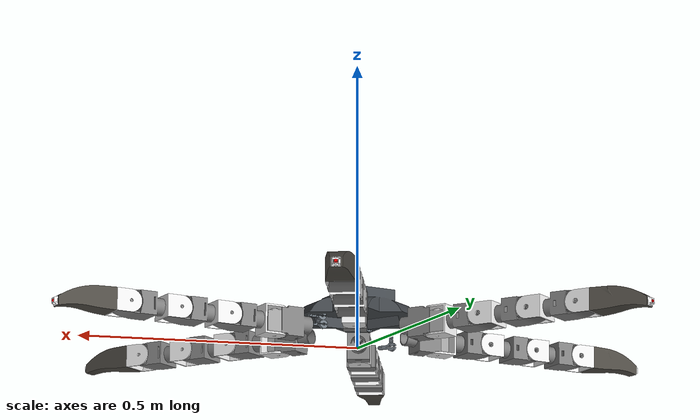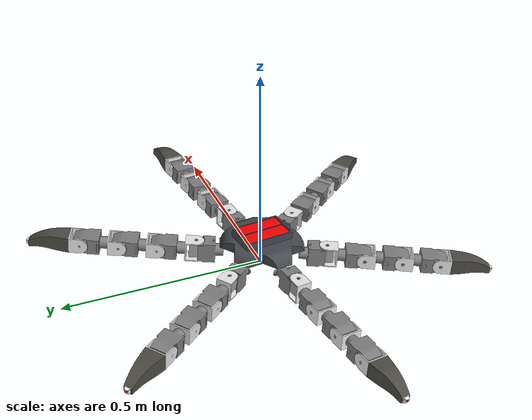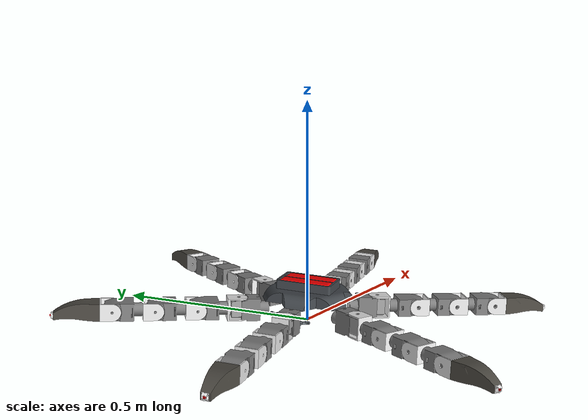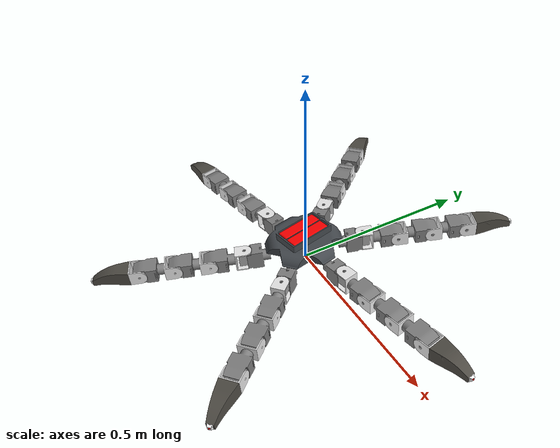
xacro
<?xml version="1.0"?>
<robot name="gg_hex"  xmlns:xacro= "http://www.ros.org/wiki/xacro">
<link name="gg_head">
<visual>
<origin xyz="0.023562198419735225219 0.060799695286904251179 0.055047203654799869987" rpy="1.6298183611939731641 -0.041056855101145567355 0.16375605659172978723" />
<geometry>
<mesh filename="file://$(find gg_hex_description)/meshes/part_1.stl"/>
</geometry>
<material name="part_1_material">
<color rgba="0.43921568627450979783 0.47450980392156860699 0.50196078431372548323 1.0"/>
</material>
</visual>
<collision>
<origin xyz="0.023562198419735225219 0.060799695286904251179 0.055047203654799869987" rpy="1.6298183611939731641 -0.041056855101145567355 0.16375605659172978723" />
<geometry>
<mesh filename="file://$(find gg_hex_description)/meshes/part_1.stl"/>
</geometry>
</collision>
<visual>
<origin xyz="0.35883672673370803352 0.056023028175970587816 0.22450447391026467914" rpy="1.511774292395820174 0.041056855101145685316 -2.9778365969980629124" />
<geometry>
<mesh filename="file://$(find gg_hex_description)/meshes/mg995_v3.stl"/>
</geometry>
<material name="mg995_v3_material">
<color rgba="0.62745098039215685404 0.62745098039215685404 0.62745098039215685404 1.0"/>
</material>
</visual>
<collision>
<origin xyz="0.35883672673370803352 0.056023028175970587816 0.22450447391026467914" rpy="1.511774292395820174 0.041056855101145685316 -2.9778365969980629124" />
<geometry>
<mesh filename="file://$(find gg_hex_description)/meshes/mg995_v3.stl"/>
</geometry>
</collision>
<visual>
<origin xyz="0.067618785825018234981 0.0073717411514467668168 0.052932771556074148522" rpy="1.6298183611939731641 -0.041056855101145733888 0.16375605659173023132" />
<geometry>
<mesh filename="file://$(find gg_hex_description)/meshes/part_1.stl"/>
</geometry>
<material name="part_1_material">
<color rgba="0.43921568627450979783 0.47450980392156860699 0.50196078431372548323 1.0"/>
</material>
</visual>
<collision>
<origin xyz="0.067618785825018234981 0.0073717411514467668168 0.052932771556074148522" rpy="1.6298183611939731641 -0.041056855101145733888 0.16375605659173023132" />
<geometry>
<mesh filename="file://$(find gg_hex_description)/meshes/part_1.stl"/>
</geometry>
</collision>
<visual>
<origin xyz="-0.36999161757788517901 -0.08448126780886903997 0.19285241442139863799" rpy="1.6298183611939731641 -0.041056855101145713072 0.16375605659173067541" />
<geometry>
<mesh filename="file://$(find gg_hex_description)/meshes/mg995_v3.stl"/>
</geometry>
<material name="mg995_v3_material">
<color rgba="0.62745098039215685404 0.62745098039215685404 0.62745098039215685404 1.0"/>
</material>
</visual>
<collision>
<origin xyz="-0.36999161757788517901 -0.08448126780886903997 0.19285241442139863799" rpy="1.6298183611939731641 -0.041056855101145713072 0.16375605659173067541" />
<geometry>
<mesh filename="file://$(find gg_hex_description)/meshes/mg995_v3.stl"/>
</geometry>
</collision>
<visual>
<origin xyz="-0.24881046969856607243 -0.1272813826038171614 0.059464627146769276356" rpy="3.1382040391284218295 -0.071804211987078134238 1.1746470986379109469" />
<geometry>
<mesh filename="file://$(find gg_hex_description)/meshes/part_3.stl"/>
</geometry>
<material name="part_3_material">
<color rgba="0.26274509803921569651 0.28235294117647058432 0.30196078431372547213 1.0"/>
</material>
</visual>
<collision>
<origin xyz="-0.24881046969856607243 -0.1272813826038171614 0.059464627146769276356" rpy="3.1382040391284218295 -0.071804211987078134238 1.1746470986379109469" />
<geometry>
<mesh filename="file://$(find gg_hex_description)/meshes/part_3.stl"/>
</geometry>
</collision>
<visual>
<origin xyz="0.23820186996947737001 -0.29430221022616825932 0.19799079715707304516" rpy="1.5057047502754277168 -0.030523938227598110956 2.2603571641492261612" />
<geometry>
<mesh filename="file://$(find gg_hex_description)/meshes/mg995_v3.stl"/>
</geometry>
<material name="mg995_v3_material">
<color rgba="0.62745098039215685404 0.62745098039215685404 0.62745098039215685404 1.0"/>
</material>
</visual>
<collision>
<origin xyz="0.23820186996947737001 -0.29430221022616825932 0.19799079715707304516" rpy="1.5057047502754277168 -0.030523938227598110956 2.2603571641492261612" />
<geometry>
<mesh filename="file://$(find gg_hex_description)/meshes/mg995_v3.stl"/>
</geometry>
</collision>
<visual>
<origin xyz="0.27302831233001362277 -0.48545547262623689466 -0.21289908517482708517" rpy="1.5057047502754270507 -0.030523938227597934014 2.2603571641492261612" />
<geometry>
<mesh filename="file://$(find gg_hex_description)/meshes/part_13.stl"/>
</geometry>
<material name="part_13_material">
<color rgba="0.49803921568627451677 0.49803921568627451677 0.49803921568627451677 1.0"/>
</material>
</visual>
<collision>
<origin xyz="0.27302831233001362277 -0.48545547262623689466 -0.21289908517482708517" rpy="1.5057047502754270507 -0.030523938227597934014 2.2603571641492261612" />
<geometry>
<mesh filename="file://$(find gg_hex_description)/meshes/part_13.stl"/>
</geometry>
</collision>
<visual>
<origin xyz="0.11505741134214290955 0.33609611858568960718 0.23519212091902330641" rpy="1.5768892466724602208 0.071625747184156512981 -1.9292085952769881807" />
<geometry>
<mesh filename="file://$(find gg_hex_description)/meshes/mg995_v3.stl"/>
</geometry>
<material name="mg995_v3_material">
<color rgba="0.62745098039215685404 0.62745098039215685404 0.62745098039215685404 1.0"/>
</material>
</visual>
<collision>
<origin xyz="0.11505741134214290955 0.33609611858568960718 0.23519212091902330641" rpy="1.5768892466724602208 0.071625747184156512981 -1.9292085952769881807" />
<geometry>
<mesh filename="file://$(find gg_hex_description)/meshes/mg995_v3.stl"/>
</geometry>
</collision>
<visual>
<origin xyz="-0.043503000651091777717 0.052109635277454907643 0.012306802034991366074" rpy="-1.5768892466724604429 -0.071625747184156651759 1.2123840583128058235" />
<geometry>
<mesh filename="file://$(find gg_hex_description)/meshes/part_1.stl"/>
</geometry>
<material name="part_1_material">
<color rgba="0.43921568627450979783 0.47450980392156860699 0.50196078431372548323 1.0"/>
</material>
</visual>
<collision>
<origin xyz="-0.043503000651091777717 0.052109635277454907643 0.012306802034991366074" rpy="-1.5768892466724604429 -0.071625747184156651759 1.2123840583128058235" />
<geometry>
<mesh filename="file://$(find gg_hex_description)/meshes/part_1.stl"/>
</geometry>
</collision>
<visual>
<origin xyz="-0.55719109193495675036 0.030756913565203894412 -0.20496596696694077688" rpy="1.6298183611939738302 -0.041056855101145803277 0.1637560565917303701" />
<geometry>
<mesh filename="file://$(find gg_hex_description)/meshes/part_13.stl"/>
</geometry>
<material name="part_13_material">
<color rgba="0.49803921568627451677 0.49803921568627451677 0.49803921568627451677 1.0"/>
</material>
</visual>
<collision>
<origin xyz="-0.55719109193495675036 0.030756913565203894412 -0.20496596696694077688" rpy="1.6298183611939738302 -0.041056855101145803277 0.1637560565917303701" />
<geometry>
<mesh filename="file://$(find gg_hex_description)/meshes/part_13.stl"/>
</geometry>
</collision>
<visual>
<origin xyz="-0.25962826526215615486 0.50870531522390083357 -0.16468574087021370378" rpy="1.6358879033143658432 0.030523938227597857686 -0.88123548944056750987" />
<geometry>
<mesh filename="file://$(find gg_hex_description)/meshes/part_13.stl"/>
</geometry>
<material name="part_13_material">
<color rgba="0.49803921568627451677 0.49803921568627451677 0.49803921568627451677 1.0"/>
</material>
</visual>
<collision>
<origin xyz="-0.25962826526215615486 0.50870531522390083357 -0.16468574087021370378" rpy="1.6358879033143658432 0.030523938227597857686 -0.88123548944056750987" />
<geometry>
<mesh filename="file://$(find gg_hex_description)/meshes/part_13.stl"/>
</geometry>
</collision>
<visual>
<origin xyz="0.28400452148104893269 0.13022715876255114287 0.013468188062415606399" rpy="-3.1382040391284427017 0.071804211987079119561 -1.96694555495217549" />
<geometry>
<mesh filename="file://$(find gg_hex_description)/meshes/part_5.stl"/>
</geometry>
<material name="part_5_material">
<color rgba="1 0 0 1.0"/>
</material>
</visual>
<collision>
<origin xyz="0.28400452148104893269 0.13022715876255114287 0.013468188062415606399" rpy="-3.1382040391284427017 0.071804211987079119561 -1.96694555495217549" />
<geometry>
<mesh filename="file://$(find gg_hex_description)/meshes/part_5.stl"/>
</geometry>
</collision>
<visual>
<origin xyz="-0.067743980593275160418 -0.012603514738496537917 0.007348666654058345904" rpy="-1.5057047502754266066 0.030523938227598003403 -0.88123548944056728782" />
<geometry>
<mesh filename="file://$(find gg_hex_description)/meshes/part_1.stl"/>
</geometry>
<material name="part_1_material">
<color rgba="0.43921568627450979783 0.47450980392156860699 0.50196078431372548323 1.0"/>
</material>
</visual>
<collision>
<origin xyz="-0.067743980593275160418 -0.012603514738496537917 0.007348666654058345904" rpy="-1.5057047502754266066 0.030523938227598003403 -0.88123548944056728782" />
<geometry>
<mesh filename="file://$(find gg_hex_description)/meshes/part_1.stl"/>
</geometry>
</collision>
<visual>
<origin xyz="-0.12621230218631923625 -0.36455435821858817036 0.18216476741263998296" rpy="1.5647034069173328952 -0.071625747184156443592 1.2123840583128053794" />
<geometry>
<mesh filename="file://$(find gg_hex_description)/meshes/mg995_v3.stl"/>
</geometry>
<material name="mg995_v3_material">
<color rgba="0.62745098039215685404 0.62745098039215685404 0.62745098039215685404 1.0"/>
</material>
</visual>
<collision>
<origin xyz="-0.12621230218631923625 -0.36455435821858817036 0.18216476741263998296" rpy="1.5647034069173328952 -0.071625747184156443592 1.2123840583128053794" />
<geometry>
<mesh filename="file://$(find gg_hex_description)/meshes/mg995_v3.stl"/>
</geometry>
</collision>
<visual>
<origin xyz="-0.00067878152244781053692 -0.0039134547290471249914 0.050089068273866853287" rpy="1.6358879033143658432 0.030523938227597979117 -0.8812354894405671768" />
<geometry>
<mesh filename="file://$(find gg_hex_description)/meshes/part_1.stl"/>
</geometry>
<material name="part_1_material">
<color rgba="0.99215686274509806708 0.0039215686274509803377 0.0039215686274509803377 1.0"/>
</material>
</visual>
<collision>
<origin xyz="-0.00067878152244781053692 -0.0039134547290471249914 0.050089068273866853287" rpy="1.6358879033143658432 0.030523938227597979117 -0.8812354894405671768" />
<geometry>
<mesh filename="file://$(find gg_hex_description)/meshes/part_1.stl"/>
</geometry>
</collision>
<visual>
<origin xyz="0.57059113900280855614 -0.0075070709675392789662 -0.17261885907810015084" rpy="1.5117742923958199519 0.041056855101145608988 -2.9778365969980629124" />
<geometry>
<mesh filename="file://$(find gg_hex_description)/meshes/part_13.stl"/>
</geometry>
<material name="part_13_material">
<color rgba="0.49803921568627451677 0.49803921568627451677 0.49803921568627451677 1.0"/>
</material>
</visual>
<collision>
<origin xyz="0.57059113900280855614 -0.0075070709675392789662 -0.17261885907810015084" rpy="1.5117742923958199519 0.041056855101145608988 -2.9778365969980629124" />
<geometry>
<mesh filename="file://$(find gg_hex_description)/meshes/part_13.stl"/>
</geometry>
</collision>
<visual>
<origin xyz="-0.29086280313886869742 -0.46632348035986820323 -0.22907263911924763411" rpy="1.5647034069173328952 -0.071625747184156401959 1.2123840583128056014" />
<geometry>
<mesh filename="file://$(find gg_hex_description)/meshes/part_13.stl"/>
</geometry>
<material name="part_13_material">
<color rgba="0.49803921568627451677 0.49803921568627451677 0.49803921568627451677 1.0"/>
</material>
</visual>
<collision>
<origin xyz="-0.29086280313886869742 -0.46632348035986820323 -0.22907263911924763411" rpy="1.5647034069173328952 -0.071625747184156401959 1.2123840583128056014" />
<geometry>
<mesh filename="file://$(find gg_hex_description)/meshes/part_13.stl"/>
</geometry>
</collision>
<visual>
<origin xyz="-0.31436063384103829499 0.022208541140831157545 0.16641996175976236927" rpy="0.066192106571393530268 0.028054638248618105068 -0.84366007373370432987" />
<geometry>
<mesh filename="file://$(find gg_hex_description)/meshes/part_5.stl"/>
</geometry>
<material name="part_5_material">
<color rgba="1 0 0 1.0"/>
</material>
</visual>
<collision>
<origin xyz="-0.31436063384103829499 0.022208541140831157545 0.16641996175976236927" rpy="0.066192106571393530268 0.028054638248618105068 -0.84366007373370432987" />
<geometry>
<mesh filename="file://$(find gg_hex_description)/meshes/part_5.stl"/>
</geometry>
</collision>
<visual>
<origin xyz="-0.24935676081365351631 0.2658439705932699737 0.21936609117459024421" rpy="1.6358879033143658432 0.030523938227597979117 -0.8812354894405671768" />
<geometry>
<mesh filename="file://$(find gg_hex_description)/meshes/mg995_v3.stl"/>
</geometry>
<material name="mg995_v3_material">
<color rgba="0.62745098039215685404 0.62745098039215685404 0.62745098039215685404 1.0"/>
</material>
</visual>
<collision>
<origin xyz="-0.24935676081365351631 0.2658439705932699737 0.21936609117459024421" rpy="1.6358879033143658432 0.030523938227597979117 -0.8812354894405671768" />
<geometry>
<mesh filename="file://$(find gg_hex_description)/meshes/mg995_v3.stl"/>
</geometry>
</collision>
<visual>
<origin xyz="-0.024919761464630933029 -0.068626604744998473406 0.045130932892933850464" rpy="1.5117742923958199519 0.041056855101145720011 -2.9778365969980629124" />
<geometry>
<mesh filename="file://$(find gg_hex_description)/meshes/part_1.stl"/>
</geometry>
<material name="part_1_material">
<color rgba="0.43921568627450979783 0.47450980392156860699 0.50196078431372548323 1.0"/>
</material>
</visual>
<collision>
<origin xyz="-0.024919761464630933029 -0.068626604744998473406 0.045130932892933850464" rpy="1.5117742923958199519 0.041056855101145720011 -2.9778365969980629124" />
<geometry>
<mesh filename="file://$(find gg_hex_description)/meshes/part_1.stl"/>
</geometry>
</collision>
<visual>
<origin xyz="0.043377805882835185347 -0.057341408864504603282 0.047974636175141138761" rpy="1.6298183611939733861 -0.041056855101145720011 0.16375605659173003703" />
<geometry>
<mesh filename="file://$(find gg_hex_description)/meshes/part_1.stl"/>
</geometry>
<material name="part_1_material">
<color rgba="0.43921568627450979783 0.47450980392156860699 0.50196078431372548323 1.0"/>
</material>
</visual>
<collision>
<origin xyz="0.043377805882835185347 -0.057341408864504603282 0.047974636175141138761" rpy="1.6298183611939733861 -0.041056855101145720011 0.16375605659173003703" />
<geometry>
<mesh filename="file://$(find gg_hex_description)/meshes/part_1.stl"/>
</geometry>
</collision>
<visual>
<origin xyz="0.30426285020672350079 0.48957332295752870044 -0.14851218692579337688" rpy="1.5768892466724602208 0.071625747184156554614 -1.9292085952769881807" />
<geometry>
<mesh filename="file://$(find gg_hex_description)/meshes/part_13.stl"/>
</geometry>
<material name="part_13_material">
<color rgba="0.49803921568627451677 0.49803921568627451677 0.49803921568627451677 1.0"/>
</material>
</visual>
<collision>
<origin xyz="0.30426285020672350079 0.48957332295752870044 -0.14851218692579337688" rpy="1.5768892466724602208 0.071625747184156554614 -1.9292085952769881807" />
<geometry>
<mesh filename="file://$(find gg_hex_description)/meshes/part_13.stl"/>
</geometry>
</collision>
<inertial>
<origin xyz="-0.00033492075222329580368 -0.0027766944231500901782 0.037897220879791443382" rpy="0 0 0"/>
<mass value="1.2784264529325646276" />
<inertia ixx="0.0034490153936869920141" ixy="2.8595055435070616551e-05"  ixz="-5.8954517689592235647e-05" iyy="0.0033407825590690528109" iyz="-0.00015297537439560451671" izz="0.0053798596339990284801" />
</inertial>
</link>

<link name="gg_leg_base">
<visual>
<origin xyz="-0.30299741173027883168 -0.21949999999999861289 -0.015497759461400667513" rpy="-5.0253421184528995419e-15 4.6851453201714274325e-15 -7.4980755101727397529e-17" />
<geometry>
<mesh filename="file://$(find gg_hex_description)/meshes/part_11.stl"/>
</geometry>
<material name="part_11_material">
<color rgba="0.49803921568627451677 0.49803921568627451677 0.49803921568627451677 1.0"/>
</material>
</visual>
<collision>
<origin xyz="-0.30299741173027883168 -0.21949999999999861289 -0.015497759461400667513" rpy="-5.0253421184528995419e-15 4.6851453201714274325e-15 -7.4980755101727397529e-17" />
<geometry>
<mesh filename="file://$(find gg_hex_description)/meshes/part_11.stl"/>
</geometry>
</collision>
<visual>
<origin xyz="-0.13214254961996313442 -0.010002240538597124281 -0.044999999999999998335" rpy="1.570796326794896558 8.2869376831356657326e-19 3.5892224525813561385e-17" />
<geometry>
<mesh filename="file://$(find gg_hex_description)/meshes/part_6.stl"/>
</geometry>
<material name="part_6_material">
<color rgba="0.91764705882352937127 0.91764705882352937127 0.91764705882352937127 1.0"/>
</material>
</visual>
<collision>
<origin xyz="-0.13214254961996313442 -0.010002240538597124281 -0.044999999999999998335" rpy="1.570796326794896558 8.2869376831356657326e-19 3.5892224525813561385e-17" />
<geometry>
<mesh filename="file://$(find gg_hex_description)/meshes/part_6.stl"/>
</geometry>
</collision>
<visual>
<origin xyz="-0.30390026077865128773 0.17899999999999885447 -0.015497759461402728365" rpy="-5.3574951067642062397e-15 4.6850915602257683286e-15 -7.4906607378984226178e-17" />
<geometry>
<mesh filename="file://$(find gg_hex_description)/meshes/mg995_v3.stl"/>
</geometry>
<material name="mg995_v3_material">
<color rgba="0.62745098039215685404 0.62745098039215685404 0.62745098039215685404 1.0"/>
</material>
</visual>
<collision>
<origin xyz="-0.30390026077865128773 0.17899999999999885447 -0.015497759461402728365" rpy="-5.3574951067642062397e-15 4.6850915602257683286e-15 -7.4906607378984226178e-17" />
<geometry>
<mesh filename="file://$(find gg_hex_description)/meshes/mg995_v3.stl"/>
</geometry>
</collision>
<inertial>
<origin xyz="-0.063706673597089258365 -0.00036253314902457892512 -0.025527945142445475357" rpy="0 0 0"/>
<mass value="0.084196217898659775347" />
<inertia ixx="2.7957377169670004607e-05" ixy="-7.7137426145814958915e-07"  ixz="1.840367732515701544e-07" iyy="9.780504909828160922e-05" iyz="3.2099813098547164346e-09" izz="9.8669146380222044171e-05" />
</inertial>
</link>

<link name="gg_leg_middle">
<visual>
<origin xyz="-0.30299741173028688079 -0.010002240538597641228 -0.24500000000000843325" rpy="1.5707963267948970021 -3.9384198187778468309e-15 -8.6579205855336464788e-17" />
<geometry>
<mesh filename="file://$(find gg_hex_description)/meshes/part_11.stl"/>
</geometry>
<material name="part_11_material">
<color rgba="0.49803921568627451677 0.49803921568627451677 0.49803921568627451677 1.0"/>
</material>
</visual>
<collision>
<origin xyz="-0.30299741173028688079 -0.010002240538597641228 -0.24500000000000843325" rpy="1.5707963267948970021 -3.9384198187778468309e-15 -8.6579205855336464788e-17" />
<geometry>
<mesh filename="file://$(find gg_hex_description)/meshes/part_11.stl"/>
</geometry>
</collision>
<visual>
<origin xyz="-0.13214254961996318993 -0.010002240538597113872 -0.044999999999999998335" rpy="1.570796326794896558 1.4408610146923778449e-17 4.2418518043364429654e-20" />
<geometry>
<mesh filename="file://$(find gg_hex_description)/meshes/part_6.stl"/>
</geometry>
<material name="part_6_material">
<color rgba="0.91764705882352937127 0.91764705882352937127 0.91764705882352937127 1.0"/>
</material>
</visual>
<collision>
<origin xyz="-0.13214254961996318993 -0.010002240538597113872 -0.044999999999999998335" rpy="1.570796326794896558 1.4408610146923778449e-17 4.2418518043364429654e-20" />
<geometry>
<mesh filename="file://$(find gg_hex_description)/meshes/part_6.stl"/>
</geometry>
</collision>
<visual>
<origin xyz="-0.30390026077866244547 -0.010002240538597058361 0.15350000000000513234" rpy="1.57079632679489678 -3.9392624646082552127e-15 -1.0737796758517056581e-16" />
<geometry>
<mesh filename="file://$(find gg_hex_description)/meshes/mg995_v3.stl"/>
</geometry>
<material name="mg995_v3_material">
<color rgba="0.62745098039215685404 0.62745098039215685404 0.62745098039215685404 1.0"/>
</material>
</visual>
<collision>
<origin xyz="-0.30390026077866244547 -0.010002240538597058361 0.15350000000000513234" rpy="1.57079632679489678 -3.9392624646082552127e-15 -1.0737796758517056581e-16" />
<geometry>
<mesh filename="file://$(find gg_hex_description)/meshes/mg995_v3.stl"/>
</geometry>
</collision>
<inertial>
<origin xyz="-0.063706673597090215933 -3.8498478453911011491e-06 -0.025894328139315591492" rpy="0 0 0"/>
<mass value="0.084196217898659775347" />
<inertia ixx="2.7955415541967256127e-05" ixy="-1.3492807390216422311e-08"  ixz="-6.0083029559715560619e-07" iyy="0.00010348466964737928282" iyz="-2.2291674578210084908e-09" izz="9.2987564203429265712e-05" />
</inertial>
</link>

<link name="gg_leg_middle_2">
<visual>
<origin xyz="-0.3029974117302809411 -0.010002240538597117342 -0.24500000000000110578" rpy="1.570796326794896558 -8.7241370779410986088e-16 -8.347377830249745191e-17" />
<geometry>
<mesh filename="file://$(find gg_hex_description)/meshes/part_11.stl"/>
</geometry>
<material name="part_11_material">
<color rgba="0.49803921568627451677 0.49803921568627451677 0.49803921568627451677 1.0"/>
</material>
</visual>
<collision>
<origin xyz="-0.3029974117302809411 -0.010002240538597117342 -0.24500000000000110578" rpy="1.570796326794896558 -8.7241370779410986088e-16 -8.347377830249745191e-17" />
<geometry>
<mesh filename="file://$(find gg_hex_description)/meshes/part_11.stl"/>
</geometry>
</collision>
<visual>
<origin xyz="-0.13214254961996307891 -0.010002240538597117342 -0.04500000000000002609" rpy="1.570796326794896558 -4.4737067079761074113e-17 5.9433632452655034867e-18" />
<geometry>
<mesh filename="file://$(find gg_hex_description)/meshes/part_6.stl"/>
</geometry>
<material name="part_6_material">
<color rgba="0.91764705882352937127 0.91764705882352937127 0.91764705882352937127 1.0"/>
</material>
</visual>
<collision>
<origin xyz="-0.13214254961996307891 -0.010002240538597117342 -0.04500000000000002609" rpy="1.570796326794896558 -4.4737067079761074113e-17 5.9433632452655034867e-18" />
<geometry>
<mesh filename="file://$(find gg_hex_description)/meshes/part_6.stl"/>
</geometry>
</collision>
<visual>
<origin xyz="-0.30390026077865706089 -0.010002240538597158975 0.15350000000000035838" rpy="1.570796326794896558 -8.4511652895505655139e-16 -8.3491698284384542985e-17" />
<geometry>
<mesh filename="file://$(find gg_hex_description)/meshes/mg995_v3.stl"/>
</geometry>
<material name="mg995_v3_material">
<color rgba="0.62745098039215685404 0.62745098039215685404 0.62745098039215685404 1.0"/>
</material>
</visual>
<collision>
<origin xyz="-0.30390026077865706089 -0.010002240538597158975 0.15350000000000035838" rpy="1.570796326794896558 -8.4511652895505655139e-16 -8.3491698284384542985e-17" />
<geometry>
<mesh filename="file://$(find gg_hex_description)/meshes/mg995_v3.stl"/>
</geometry>
</collision>
<inertial>
<origin xyz="-0.063706673597089619188 -3.849847845403463595e-06 -0.0258943281393156019" rpy="0 0 0"/>
<mass value="0.084196217898659775347" />
<inertia ixx="2.7955415541966429423e-05" ixy="-1.3492807390220369617e-08"  ixz="-6.0083029559718969926e-07" iyy="0.0001034846696473767214" iyz="-2.2291674578647861975e-09" izz="9.2987564203426406129e-05" />
</inertial>
</link>

<link name="gg_leg_tip">
<visual>
<origin xyz="-0.13214254961996307891 -0.010002240538597117342 -0.044999999999999998335" rpy="1.570796326794896558 -1.904150047884730158e-18 -4.1795962113096593812e-18" />
<geometry>
<mesh filename="file://$(find gg_hex_description)/meshes/part_6.stl"/>
</geometry>
<material name="part_6_material">
<color rgba="0.91764705882352937127 0.91764705882352937127 0.91764705882352937127 1.0"/>
</material>
</visual>
<collision>
<origin xyz="-0.13214254961996307891 -0.010002240538597117342 -0.044999999999999998335" rpy="1.570796326794896558 -1.904150047884730158e-18 -4.1795962113096593812e-18" />
<geometry>
<mesh filename="file://$(find gg_hex_description)/meshes/part_6.stl"/>
</geometry>
</collision>
<visual>
<origin xyz="-0.12259448999999977836 0.00980317120259485697 -0.025281761415826411316" rpy="-1.5707963267948861219 1.5707963267948956698 0" />
<geometry>
<mesh filename="file://$(find gg_hex_description)/meshes/led_3mm_trans.stl"/>
</geometry>
<material name="led_3mm_trans_material">
<color rgba="1 1 1 1.0"/>
</material>
</visual>
<collision>
<origin xyz="-0.12259448999999977836 0.00980317120259485697 -0.025281761415826411316" rpy="-1.5707963267948861219 1.5707963267948956698 0" />
<geometry>
<mesh filename="file://$(find gg_hex_description)/meshes/led_3mm_trans.stl"/>
</geometry>
</collision>
<visual>
<origin xyz="-0.12029448999999980963 0.010865472711805306688 -0.024348211468834146665" rpy="3.1415926535897895633 -6.148005069071422886e-19 -1.5707963267949054398" />
<geometry>
<mesh filename="file://$(find gg_hex_description)/meshes/pulsador.stl"/>
</geometry>
<material name="pulsador_material">
<color rgba="1 0 0 1.0"/>
</material>
</visual>
<collision>
<origin xyz="-0.12029448999999980963 0.010865472711805306688 -0.024348211468834146665" rpy="3.1415926535897895633 -6.148005069071422886e-19 -1.5707963267949054398" />
<geometry>
<mesh filename="file://$(find gg_hex_description)/meshes/pulsador.stl"/>
</geometry>
</collision>
<visual>
<origin xyz="-0.026494489999999815133 0.14717946631848960459 -0.050978735407716677108" rpy="3.141592653589793116 -1.5635714428690265754e-17 1.5707963267948950037" />
<geometry>
<mesh filename="file://$(find gg_hex_description)/meshes/part_25.stl"/>
</geometry>
<material name="part_25_material">
<color rgba="0.30196078431372547213 0.29019607843137257275 0.26274509803921569651 1.0"/>
</material>
</visual>
<collision>
<origin xyz="-0.026494489999999815133 0.14717946631848960459 -0.050978735407716677108" rpy="3.141592653589793116 -1.5635714428690265754e-17 1.5707963267948950037" />
<geometry>
<mesh filename="file://$(find gg_hex_description)/meshes/part_25.stl"/>
</geometry>
</collision>
<inertial>
<origin xyz="-0.058600447713097608693 0.00030798747790676935182 -0.025499135322571444412" rpy="0 0 0"/>
<mass value="0.15555503524263536441" />
<inertia ixx="4.2100962384745876563e-05" ixy="5.2877209940368932904e-06"  ixz="2.0615243018228742286e-07" iyy="0.00015940278081236355315" iyz="2.8650165663793950556e-08" izz="0.00015063387305897928429" />
</inertial>
</link>

<joint name="lm4" type="revolute">
<origin xyz="-0.093900260629644682897 -2.2405385971223379382e-06 2.0816681711721685133e-17" rpy="8.9121431276618812356e-17 1.6457097233569706371e-16 -1.1012511844409759687e-15" />
<parent link="gg_leg_middle_2" />
<child link="gg_leg_tip" />
<axis xyz="0 0 1"/>
<limit effort="1" velocity="20" lower="-1.570796326794896558" upper="1.570796326794896558"/>
<joint_properties friction="0.0"/>
</joint>

<joint name="lm3" type="revolute">
<origin xyz="-0.093900260629645626587 -2.2405385970737656809e-06 7.0429773124658368033e-16" rpy="-1.4364032458127833465e-15 8.3071497518661454773e-16 -5.7454177686472719623e-16" />
<parent link="gg_leg_middle" />
<child link="gg_leg_middle_2" />
<axis xyz="0 0 1"/>
<limit effort="1" velocity="20" lower="-1.570796326794896558" upper="1.570796326794896558"/>
<joint_properties friction="0.0"/>
</joint>

<joint name="lm2" type="revolute">
<origin xyz="-0.093900260629643572674 0.025499999999999838768 -0.025497759461402813574" rpy="-1.5707963267949018871 4.8235110386661821187e-15 1.3983679418769673769e-15" />
<parent link="gg_leg_base" />
<child link="gg_leg_middle" />
<axis xyz="0 0 1"/>
<limit effort="1" velocity="20" lower="-1.570796326794896558" upper="1.570796326794896558"/>
<joint_properties friction="0.0"/>
</joint>

<joint name="lm1" type="revolute">
<origin xyz="-0.15989770560276919675 -0.030470909749676838851 0.048957732671533575608" rpy="0.059022034399081720057 -0.041056855101150903364 0.16375605659172964845" />
<parent link="gg_head" />
<child link="gg_leg_base" />
<axis xyz="0 0 1"/>
<limit effort="1" velocity="20" lower="-1.570796326794896558" upper="1.570796326794896558"/>
<joint_properties friction="0.0"/>
</joint>

<link name="gg_leg_base_2">
<visual>
<origin xyz="-0.30299741173027416874 -0.21949999999999550426 -0.015497759461403443071" rpy="9.08892954557665105e-16 -1.1348655322675221538e-15 -3.986100168139387931e-16" />
<geometry>
<mesh filename="file://$(find gg_hex_description)/meshes/part_11.stl"/>
</geometry>
<material name="part_11_material">
<color rgba="0.49803921568627451677 0.49803921568627451677 0.49803921568627451677 1.0"/>
</material>
</visual>
<collision>
<origin xyz="-0.30299741173027416874 -0.21949999999999550426 -0.015497759461403443071" rpy="9.08892954557665105e-16 -1.1348655322675221538e-15 -3.986100168139387931e-16" />
<geometry>
<mesh filename="file://$(find gg_hex_description)/meshes/part_11.stl"/>
</geometry>
</collision>
<visual>
<origin xyz="-0.13214254961996318993 -0.010002240538597093056 -0.044999999999999998335" rpy="1.570796326794896558 1.7889197704395807258e-18 -4.4005512212866888487e-17" />
<geometry>
<mesh filename="file://$(find gg_hex_description)/meshes/part_6.stl"/>
</geometry>
<material name="part_6_material">
<color rgba="0.91764705882352937127 0.91764705882352937127 0.91764705882352937127 1.0"/>
</material>
</visual>
<collision>
<origin xyz="-0.13214254961996318993 -0.010002240538597093056 -0.044999999999999998335" rpy="1.570796326794896558 1.7889197704395807258e-18 -4.4005512212866888487e-17" />
<geometry>
<mesh filename="file://$(find gg_hex_description)/meshes/part_6.stl"/>
</geometry>
</collision>
<visual>
<origin xyz="-0.30390026077864923382 0.17899999999999663403 -0.015497759461403151637" rpy="6.1824788979659292879e-16 -1.1348655322675221538e-15 -3.986100168139387931e-16" />
<geometry>
<mesh filename="file://$(find gg_hex_description)/meshes/mg995_v3.stl"/>
</geometry>
<material name="mg995_v3_material">
<color rgba="0.62745098039215685404 0.62745098039215685404 0.62745098039215685404 1.0"/>
</material>
</visual>
<collision>
<origin xyz="-0.30390026077864923382 0.17899999999999663403 -0.015497759461403151637" rpy="6.1824788979659292879e-16 -1.1348655322675221538e-15 -3.986100168139387931e-16" />
<geometry>
<mesh filename="file://$(find gg_hex_description)/meshes/mg995_v3.stl"/>
</geometry>
</collision>
<inertial>
<origin xyz="-0.063706673597088939176 -0.00036253314902449175526 -0.025527945142445614135" rpy="0 0 0"/>
<mass value="0.084196217898659775347" />
<inertia ixx="2.7957377169669537045e-05" ixy="-7.713742614582091991e-07"  ixz="1.8403677325144508469e-07" iyy="9.7805049098279955811e-05" iyz="3.2099813100055987278e-09" izz="9.8669146380221054837e-05" />
</inertial>
</link>

<link name="gg_leg_middle_3">
<visual>
<origin xyz="-0.3029974117302799419 -0.010002240538597120811 -0.24499999999999941269" rpy="1.570796326794896558 2.2646934460469713581e-15 -7.5305902707547660527e-17" />
<geometry>
<mesh filename="file://$(find gg_hex_description)/meshes/part_11.stl"/>
</geometry>
<material name="part_11_material">
<color rgba="0.49803921568627451677 0.49803921568627451677 0.49803921568627451677 1.0"/>
</material>
</visual>
<collision>
<origin xyz="-0.3029974117302799419 -0.010002240538597120811 -0.24499999999999941269" rpy="1.570796326794896558 2.2646934460469713581e-15 -7.5305902707547660527e-17" />
<geometry>
<mesh filename="file://$(find gg_hex_description)/meshes/part_11.stl"/>
</geometry>
</collision>
<visual>
<origin xyz="-0.13214254961996313442 -0.010002240538597106934 -0.044999999999999956701" rpy="1.570796326794896558 2.8811852914727892284e-17 1.0667301901496596253e-18" />
<geometry>
<mesh filename="file://$(find gg_hex_description)/meshes/part_6.stl"/>
</geometry>
<material name="part_6_material">
<color rgba="0.91764705882352937127 0.91764705882352937127 0.91764705882352937127 1.0"/>
</material>
</visual>
<collision>
<origin xyz="-0.13214254961996313442 -0.010002240538597106934 -0.044999999999999956701" rpy="1.570796326794896558 2.8811852914727892284e-17 1.0667301901496596253e-18" />
<geometry>
<mesh filename="file://$(find gg_hex_description)/meshes/part_6.stl"/>
</geometry>
</collision>
<visual>
<origin xyz="-0.30390026077865528453 -0.010002240538597016728 0.15350000000000066369" rpy="1.570796326794896558 2.2651430761290183205e-15 -6.8384928785527486247e-17" />
<geometry>
<mesh filename="file://$(find gg_hex_description)/meshes/mg995_v3.stl"/>
</geometry>
<material name="mg995_v3_material">
<color rgba="0.62745098039215685404 0.62745098039215685404 0.62745098039215685404 1.0"/>
</material>
</visual>
<collision>
<origin xyz="-0.30390026077865528453 -0.010002240538597016728 0.15350000000000066369" rpy="1.570796326794896558 2.2651430761290183205e-15 -6.8384928785527486247e-17" />
<geometry>
<mesh filename="file://$(find gg_hex_description)/meshes/mg995_v3.stl"/>
</geometry>
</collision>
<inertial>
<origin xyz="-0.063706673597089549799 -3.8498478453866957308e-06 -0.025894328139315428428" rpy="0 0 0"/>
<mass value="0.084196217898659775347" />
<inertia ixx="2.7955415541966202418e-05" ixy="-1.3492807390222373048e-08"  ixz="-6.0083029559703903328e-07" iyy="0.00010348466964737597601" iyz="-2.2291674578595629655e-09" izz="9.2987564203425836923e-05" />
</inertial>
</link>

<link name="gg_leg_middle_4">
<visual>
<origin xyz="-0.30299741173027583407 -0.010002240538596825908 -0.24499999999999744205" rpy="1.5707963267948958919 -4.0429786383155117073e-15 -9.4758539164312868187e-17" />
<geometry>
<mesh filename="file://$(find gg_hex_description)/meshes/part_11.stl"/>
</geometry>
<material name="part_11_material">
<color rgba="0.49803921568627451677 0.49803921568627451677 0.49803921568627451677 1.0"/>
</material>
</visual>
<collision>
<origin xyz="-0.30299741173027583407 -0.010002240538596825908 -0.24499999999999744205" rpy="1.5707963267948958919 -4.0429786383155117073e-15 -9.4758539164312868187e-17" />
<geometry>
<mesh filename="file://$(find gg_hex_description)/meshes/part_11.stl"/>
</geometry>
</collision>
<visual>
<origin xyz="-0.13214254961996318993 -0.010002240538597117342 -0.044999999999999998335" rpy="1.570796326794896558 -5.6482975450038743564e-18 2.1765768202793749203e-19" />
<geometry>
<mesh filename="file://$(find gg_hex_description)/meshes/part_6.stl"/>
</geometry>
<material name="part_6_material">
<color rgba="0.91764705882352937127 0.91764705882352937127 0.91764705882352937127 1.0"/>
</material>
</visual>
<collision>
<origin xyz="-0.13214254961996318993 -0.010002240538597117342 -0.044999999999999998335" rpy="1.570796326794896558 -5.6482975450038743564e-18 2.1765768202793749203e-19" />
<geometry>
<mesh filename="file://$(find gg_hex_description)/meshes/part_6.stl"/>
</geometry>
</collision>
<visual>
<origin xyz="-0.30390026077865217591 -0.010002240538596978564 0.15349999999999608402" rpy="1.5707963267948956698 -4.027751960261554391e-15 -7.7465064350206378616e-17" />
<geometry>
<mesh filename="file://$(find gg_hex_description)/meshes/mg995_v3.stl"/>
</geometry>
<material name="mg995_v3_material">
<color rgba="0.62745098039215685404 0.62745098039215685404 0.62745098039215685404 1.0"/>
</material>
</visual>
<collision>
<origin xyz="-0.30390026077865217591 -0.010002240538596978564 0.15349999999999608402" rpy="1.5707963267948956698 -4.027751960261554391e-15 -7.7465064350206378616e-17" />
<geometry>
<mesh filename="file://$(find gg_hex_description)/meshes/mg995_v3.stl"/>
</geometry>
</collision>
<inertial>
<origin xyz="-0.06370667359708923061 -3.8498478453867084363e-06 -0.025894328139315612308" rpy="0 0 0"/>
<mass value="0.084196217898659775347" />
<inertia ixx="2.7955415541965677258e-05" ixy="-1.3492807390269251028e-08"  ixz="-6.0083029559715179454e-07" iyy="0.00010348466964737402444" iyz="-2.2291674578960809216e-09" izz="9.2987564203423939569e-05" />
</inertial>
</link>

<link name="gg_leg_tip_2">
<visual>
<origin xyz="-0.1321425496199630234 -0.010002240538597106934 -0.045000000000000005274" rpy="1.570796326794896558 4.4771665652153369278e-17 -1.5317743236262503331e-18" />
<geometry>
<mesh filename="file://$(find gg_hex_description)/meshes/part_6.stl"/>
</geometry>
<material name="part_6_material">
<color rgba="0.91764705882352937127 0.91764705882352937127 0.91764705882352937127 1.0"/>
</material>
</visual>
<collision>
<origin xyz="-0.1321425496199630234 -0.010002240538597106934 -0.045000000000000005274" rpy="1.570796326794896558 4.4771665652153369278e-17 -1.5317743236262503331e-18" />
<geometry>
<mesh filename="file://$(find gg_hex_description)/meshes/part_6.stl"/>
</geometry>
</collision>
<visual>
<origin xyz="-0.12259448999999827956 0.0098031712025947112532 -0.025281761415826473766" rpy="-1.5707963267948861219 1.5707963267948927832 0" />
<geometry>
<mesh filename="file://$(find gg_hex_description)/meshes/led_3mm_trans.stl"/>
</geometry>
<material name="led_3mm_trans_material">
<color rgba="1 1 1 1.0"/>
</material>
</visual>
<collision>
<origin xyz="-0.12259448999999827956 0.0098031712025947112532 -0.025281761415826473766" rpy="-1.5707963267948861219 1.5707963267948927832 0" />
<geometry>
<mesh filename="file://$(find gg_hex_description)/meshes/led_3mm_trans.stl"/>
</geometry>
</collision>
<visual>
<origin xyz="-0.12029448999999831083 0.010865472711805115869 -0.024348211468834160542" rpy="3.1415926535897900074 1.0485061603891755637e-17 -1.5707963267949005548" />
<geometry>
<mesh filename="file://$(find gg_hex_description)/meshes/pulsador.stl"/>
</geometry>
<material name="pulsador_material">
<color rgba="1 0 0 1.0"/>
</material>
</visual>
<collision>
<origin xyz="-0.12029448999999831083 0.010865472711805115869 -0.024348211468834160542" rpy="3.1415926535897900074 1.0485061603891755637e-17 -1.5707963267949005548" />
<geometry>
<mesh filename="file://$(find gg_hex_description)/meshes/pulsador.stl"/>
</geometry>
</collision>
<visual>
<origin xyz="-0.026494490000000536778 0.14717946631848757844 -0.050978735407716323225" rpy="3.141592653589793116 -1.1505811239274696774e-17 1.5707963267948996666" />
<geometry>
<mesh filename="file://$(find gg_hex_description)/meshes/part_25.stl"/>
</geometry>
<material name="part_25_material">
<color rgba="0.30196078431372547213 0.29019607843137257275 0.26274509803921569651 1.0"/>
</material>
</visual>
<collision>
<origin xyz="-0.026494490000000536778 0.14717946631848757844 -0.050978735407716323225" rpy="3.141592653589793116 -1.1505811239274696774e-17 1.5707963267948996666" />
<geometry>
<mesh filename="file://$(find gg_hex_description)/meshes/part_25.stl"/>
</geometry>
</collision>
<inertial>
<origin xyz="-0.058600447713097074398 0.00030798747790677054445 -0.025499135322571447881" rpy="0 0 0"/>
<mass value="0.15555503524263536441" />
<inertia ixx="4.2100962384744860124e-05" ixy="5.2877209940362309107e-06"  ixz="2.0615243018265948208e-07" iyy="0.00015940278081235965003" iyz="2.8650165663652469584e-08" izz="0.00015063387305897538116" />
</inertial>
</link>

<joint name="lb4" type="revolute">
<origin xyz="-0.093900260629643683696 -2.2405385971119295974e-06 -6.3143934525555778237e-16" rpy="-1.4281149243277591124e-15 -3.594331694279096171e-15 9.9841486085899290693e-16" />
<parent link="gg_leg_middle_4" />
<child link="gg_leg_tip_2" />
<axis xyz="0 0 1"/>
<limit effort="1" velocity="20" lower="-1.570796326794896558" upper="1.570796326794896558"/>
<joint_properties friction="0.0"/>
</joint>

<joint name="lb3" type="revolute">
<origin xyz="-0.093900260629644294319 -2.2405385970911129156e-06 2.0469737016526323714e-16" rpy="2.3530522450755790234e-15 8.3699772542609794061e-15 2.187764900340348694e-15" />
<parent link="gg_leg_middle_3" />
<child link="gg_leg_middle_4" />
<axis xyz="0 0 1"/>
<limit effort="1" velocity="20" lower="-1.570796326794896558" upper="1.570796326794896558"/>
<joint_properties friction="0.0"/>
</joint>

<joint name="lb2" type="revolute">
<origin xyz="-0.093900260629643128585 0.025499999999999536926 -0.025497759461402945413" rpy="-1.5707963267948958919 -1.1626659078378696825e-15 -1.1226801006324084038e-15" />
<parent link="gg_leg_base_2" />
<child link="gg_leg_middle_3" />
<axis xyz="0 0 1"/>
<limit effort="1" velocity="20" lower="-1.570796326794896558" upper="1.570796326794896558"/>
<joint_properties friction="0.0"/>
</joint>

<joint name="lb1" type="revolute">
<origin xyz="-0.10337656821023745446 0.12019112043748506058 0.060503632829168214891" rpy="0.064875133408970650506 0.030981800885671175599 -0.8882747132632872189" />
<parent link="gg_head" />
<child link="gg_leg_base_2" />
<axis xyz="0 0 1"/>
<limit effort="1" velocity="20" lower="-1.570796326794896558" upper="1.570796326794896558"/>
<joint_properties friction="0.0"/>
</joint>

<link name="gg_leg_base_3">
<visual>
<origin xyz="-0.30299741173027849861 -0.2194999999999989182 -0.015497759461402894898" rpy="-6.0392996120851477923e-18 -1.3504081871806947429e-17 -6.4220696017445946548e-17" />
<geometry>
<mesh filename="file://$(find gg_hex_description)/meshes/part_11.stl"/>
</geometry>
<material name="part_11_material">
<color rgba="0.49803921568627451677 0.49803921568627451677 0.49803921568627451677 1.0"/>
</material>
</visual>
<collision>
<origin xyz="-0.30299741173027849861 -0.2194999999999989182 -0.015497759461402894898" rpy="-6.0392996120851477923e-18 -1.3504081871806947429e-17 -6.4220696017445946548e-17" />
<geometry>
<mesh filename="file://$(find gg_hex_description)/meshes/part_11.stl"/>
</geometry>
</collision>
<visual>
<origin xyz="-0.13214254961996313442 -0.010002240538597108668 -0.045000000000000005274" rpy="1.570796326794896558 -5.9397308589417467453e-19 -2.4681096358802447301e-18" />
<geometry>
<mesh filename="file://$(find gg_hex_description)/meshes/part_6.stl"/>
</geometry>
<material name="part_6_material">
<color rgba="0.91764705882352937127 0.91764705882352937127 0.91764705882352937127 1.0"/>
</material>
</visual>
<collision>
<origin xyz="-0.13214254961996313442 -0.010002240538597108668 -0.045000000000000005274" rpy="1.570796326794896558 -5.9397308589417467453e-19 -2.4681096358802447301e-18" />
<geometry>
<mesh filename="file://$(find gg_hex_description)/meshes/part_6.stl"/>
</geometry>
</collision>
<visual>
<origin xyz="-0.30390026077865478493 0.17899999999999913203 -0.01549775946140288102" rpy="1.6398512231923365155e-16 -6.8907713211742627054e-17 7.8980521185812035702e-17" />
<geometry>
<mesh filename="file://$(find gg_hex_description)/meshes/mg995_v3.stl"/>
</geometry>
<material name="mg995_v3_material">
<color rgba="0.62745098039215685404 0.62745098039215685404 0.62745098039215685404 1.0"/>
</material>
</visual>
<collision>
<origin xyz="-0.30390026077865478493 0.17899999999999913203 -0.01549775946140288102" rpy="1.6398512231923365155e-16 -6.8907713211742627054e-17 7.8980521185812035702e-17" />
<geometry>
<mesh filename="file://$(find gg_hex_description)/meshes/mg995_v3.stl"/>
</geometry>
</collision>
<inertial>
<origin xyz="-0.063706673597089438776 -0.00036253314902456819152 -0.025527945142445589849" rpy="0 0 0"/>
<mass value="0.084196217898659775347" />
<inertia ixx="2.7957377169670265493e-05" ixy="-7.7137426145837489992e-07"  ixz="1.8403677325150257705e-07" iyy="9.7805049098282097111e-05" iyz="3.2099813099583336276e-09" izz="9.866914638022289798e-05" />
</inertial>
</link>

<link name="gg_leg_middle_5">
<visual>
<origin xyz="-0.30299741173028726937 -0.010002240538597464287 -0.24500000000000432543" rpy="1.5707963267948972241 1.1047616710797734841e-14 -8.1613261303240950597e-17" />
<geometry>
<mesh filename="file://$(find gg_hex_description)/meshes/part_11.stl"/>
</geometry>
<material name="part_11_material">
<color rgba="0.49803921568627451677 0.49803921568627451677 0.49803921568627451677 1.0"/>
</material>
</visual>
<collision>
<origin xyz="-0.30299741173028726937 -0.010002240538597464287 -0.24500000000000432543" rpy="1.5707963267948972241 1.1047616710797734841e-14 -8.1613261303240950597e-17" />
<geometry>
<mesh filename="file://$(find gg_hex_description)/meshes/part_11.stl"/>
</geometry>
</collision>
<visual>
<origin xyz="-0.13214254961996307891 -0.010002240538597110403 -0.044999999999999984457" rpy="1.570796326794896558 4.6438835783601596915e-17 6.9577801822130106963e-18" />
<geometry>
<mesh filename="file://$(find gg_hex_description)/meshes/part_6.stl"/>
</geometry>
<material name="part_6_material">
<color rgba="0.91764705882352937127 0.91764705882352937127 0.91764705882352937127 1.0"/>
</material>
</visual>
<collision>
<origin xyz="-0.13214254961996307891 -0.010002240538597110403 -0.044999999999999984457" rpy="1.570796326794896558 4.6438835783601596915e-17 6.9577801822130106963e-18" />
<geometry>
<mesh filename="file://$(find gg_hex_description)/meshes/part_6.stl"/>
</geometry>
</collision>
<visual>
<origin xyz="-0.30390026077866338916 -0.010002240538597429592 0.15350000000000876832" rpy="1.5707963267948972241 1.0980396176103635144e-14 -8.1613261303240950597e-17" />
<geometry>
<mesh filename="file://$(find gg_hex_description)/meshes/mg995_v3.stl"/>
</geometry>
<material name="mg995_v3_material">
<color rgba="0.62745098039215685404 0.62745098039215685404 0.62745098039215685404 1.0"/>
</material>
</visual>
<collision>
<origin xyz="-0.30390026077866338916 -0.010002240538597429592 0.15350000000000876832" rpy="1.5707963267948972241 1.0980396176103635144e-14 -8.1613261303240950597e-17" />
<geometry>
<mesh filename="file://$(find gg_hex_description)/meshes/mg995_v3.stl"/>
</geometry>
</collision>
<inertial>
<origin xyz="-0.063706673597090118788 -3.8498478453974284853e-06 -0.0258943281393152272" rpy="0 0 0"/>
<mass value="0.084196217898659775347" />
<inertia ixx="2.7955415541967374712e-05" ixy="-1.3492807390267699237e-08"  ixz="-6.0083029559688169691e-07" iyy="0.00010348466964738009598" iyz="-2.2291674578448242614e-09" izz="9.298756420342936058e-05" />
</inertial>
</link>

<link name="gg_leg_middle_6">
<visual>
<origin xyz="-0.30299741173027266994 -0.010002240538596676722 -0.24499999999999574896" rpy="1.570796326794896558 -1.1409721248348754892e-14 -9.1979484934263985836e-17" />
<geometry>
<mesh filename="file://$(find gg_hex_description)/meshes/part_11.stl"/>
</geometry>
<material name="part_11_material">
<color rgba="0.49803921568627451677 0.49803921568627451677 0.49803921568627451677 1.0"/>
</material>
</visual>
<collision>
<origin xyz="-0.30299741173027266994 -0.010002240538596676722 -0.24499999999999574896" rpy="1.570796326794896558 -1.1409721248348754892e-14 -9.1979484934263985836e-17" />
<geometry>
<mesh filename="file://$(find gg_hex_description)/meshes/part_11.stl"/>
</geometry>
</collision>
<visual>
<origin xyz="-0.13214254961996313442 -0.010002240538597113872 -0.045000000000000019151" rpy="1.570796326794896558 -1.415996071785062598e-17 -4.2600462839941285862e-19" />
<geometry>
<mesh filename="file://$(find gg_hex_description)/meshes/part_6.stl"/>
</geometry>
<material name="part_6_material">
<color rgba="0.91764705882352937127 0.91764705882352937127 0.91764705882352937127 1.0"/>
</material>
</visual>
<collision>
<origin xyz="-0.13214254961996313442 -0.010002240538597113872 -0.045000000000000019151" rpy="1.570796326794896558 -1.415996071785062598e-17 -4.2600462839941285862e-19" />
<geometry>
<mesh filename="file://$(find gg_hex_description)/meshes/part_6.stl"/>
</geometry>
</collision>
<visual>
<origin xyz="-0.30390026077864845666 -0.010002240538596843256 0.15349999999999117128" rpy="1.570796326794896336 -1.1512048386547029668e-14 -2.2662225822738969349e-17" />
<geometry>
<mesh filename="file://$(find gg_hex_description)/meshes/mg995_v3.stl"/>
</geometry>
<material name="mg995_v3_material">
<color rgba="0.62745098039215685404 0.62745098039215685404 0.62745098039215685404 1.0"/>
</material>
</visual>
<collision>
<origin xyz="-0.30390026077864845666 -0.010002240538596843256 0.15349999999999117128" rpy="1.570796326794896336 -1.1512048386547029668e-14 -2.2662225822738969349e-17" />
<geometry>
<mesh filename="file://$(find gg_hex_description)/meshes/mg995_v3.stl"/>
</geometry>
</collision>
<inertial>
<origin xyz="-0.063706673597088814276 -3.8498478454037575154e-06 -0.025894328139315751086" rpy="0 0 0"/>
<mass value="0.084196217898659775347" />
<inertia ixx="2.7955415541965185979e-05" ixy="-1.349280739018826012e-08"  ixz="-6.0083029559720113421e-07" iyy="0.00010348466964737193735" iyz="-2.2291674578789458752e-09" izz="9.2987564203422150635e-05" />
</inertial>
</link>

<link name="gg_leg_tip_3">
<visual>
<origin xyz="-0.13214254961996307891 -0.010002240538597106934 -0.045000000000000019151" rpy="1.570796326794896558 -3.8270440748095850673e-17 2.8051376661262384383e-18" />
<geometry>
<mesh filename="file://$(find gg_hex_description)/meshes/part_6.stl"/>
</geometry>
<material name="part_6_material">
<color rgba="0.91764705882352937127 0.91764705882352937127 0.91764705882352937127 1.0"/>
</material>
</visual>
<collision>
<origin xyz="-0.13214254961996307891 -0.010002240538597106934 -0.045000000000000019151" rpy="1.570796326794896558 -3.8270440748095850673e-17 2.8051376661262384383e-18" />
<geometry>
<mesh filename="file://$(find gg_hex_description)/meshes/part_6.stl"/>
</geometry>
</collision>
<visual>
<origin xyz="-0.12259449000000022245 0.0098031712025948673783 -0.025281761415826414785" rpy="-1.5707963267948863439 1.5707963267948954478 0" />
<geometry>
<mesh filename="file://$(find gg_hex_description)/meshes/led_3mm_trans.stl"/>
</geometry>
<material name="led_3mm_trans_material">
<color rgba="1 1 1 1.0"/>
</material>
</visual>
<collision>
<origin xyz="-0.12259449000000022245 0.0098031712025948673783 -0.025281761415826414785" rpy="-1.5707963267948863439 1.5707963267948954478 0" />
<geometry>
<mesh filename="file://$(find gg_hex_description)/meshes/led_3mm_trans.stl"/>
</geometry>
</collision>
<visual>
<origin xyz="-0.12029449000000003167 0.010865472711805306688 -0.024348211468834150134" rpy="3.1415926535897900074 -3.9566810390488212073e-18 -1.5707963267949041075" />
<geometry>
<mesh filename="file://$(find gg_hex_description)/meshes/pulsador.stl"/>
</geometry>
<material name="pulsador_material">
<color rgba="1 0 0 1.0"/>
</material>
</visual>
<collision>
<origin xyz="-0.12029449000000003167 0.010865472711805306688 -0.024348211468834150134" rpy="3.1415926535897900074 -3.9566810390488212073e-18 -1.5707963267949041075" />
<geometry>
<mesh filename="file://$(find gg_hex_description)/meshes/pulsador.stl"/>
</geometry>
</collision>
<visual>
<origin xyz="-0.026494489999999926155 0.14717946631848993766 -0.050978735407716760375" rpy="3.141592653589793116 1.4018043663752349529e-18 1.570796326794896558" />
<geometry>
<mesh filename="file://$(find gg_hex_description)/meshes/part_25.stl"/>
</geometry>
<material name="part_25_material">
<color rgba="0.30196078431372547213 0.29019607843137257275 0.26274509803921569651 1.0"/>
</material>
</visual>
<collision>
<origin xyz="-0.026494489999999926155 0.14717946631848993766 -0.050978735407716760375" rpy="3.141592653589793116 1.4018043663752349529e-18 1.570796326794896558" />
<geometry>
<mesh filename="file://$(find gg_hex_description)/meshes/part_25.stl"/>
</geometry>
</collision>
<inertial>
<origin xyz="-0.05860044771309769196 0.00030798747790679531847 -0.025499135322571447881" rpy="0 0 0"/>
<mass value="0.15555503524263536441" />
<inertia ixx="4.2100962384746174719e-05" ixy="5.2877209940367933406e-06"  ixz="2.0615243018225280039e-07" iyy="0.00015940278081236423078" iyz="2.8650165663756095462e-08" izz="0.00015063387305898012455" />
</inertial>
</link>

<joint name="rb4" type="revolute">
<origin xyz="-0.093900260629643073074 -2.2405385971327462791e-06 -1.4051260155412137465e-15" rpy="-4.3866234899743084146e-16 -1.0387297738605973329e-14 1.8514619165673799566e-16" />
<parent link="gg_leg_middle_6" />
<child link="gg_leg_tip_3" />
<axis xyz="0 0 1"/>
<limit effort="1" velocity="20" lower="-1.570796326794896558" upper="1.570796326794896558"/>
<joint_properties friction="0.0"/>
</joint>

<joint name="rb3" type="revolute">
<origin xyz="-0.093900260629645682098 -2.2405385971188684913e-06 1.3669620990697239904e-15" rpy="7.2637737885667555047e-16 1.1374362925258319569e-14 -5.3750165796290538343e-17" />
<parent link="gg_leg_middle_5" />
<child link="gg_leg_middle_6" />
<axis xyz="0 0 1"/>
<limit effort="1" velocity="20" lower="-1.570796326794896558" upper="1.570796326794896558"/>
<joint_properties friction="0.0"/>
</joint>

<joint name="rb2" type="revolute">
<origin xyz="-0.093900260629644183297 0.02549999999999989081 -0.025497759461402889902" rpy="-1.570796326794896558 -6.8871873247968481882e-17 1.1423496803474699307e-15" />
<parent link="gg_leg_base_3" />
<child link="gg_leg_middle_5" />
<axis xyz="0 0 1"/>
<limit effort="1" velocity="20" lower="-1.570796326794896558" upper="1.570796326794896558"/>
<joint_properties friction="0.0"/>
</joint>

<joint name="rb1" type="revolute">
<origin xyz="0.055672905232045107049 0.14639174427584597526 0.067120764452921671817" rpy="0.0027364936186193263359 0.071831972774225663625 -1.9760334780445123481" />
<parent link="gg_head" />
<child link="gg_leg_base_3" />
<axis xyz="0 0 1"/>
<limit effort="1" velocity="20" lower="-1.570796326794896558" upper="1.570796326794896558"/>
<joint_properties friction="0.0"/>
</joint>

<link name="gg_leg_base_4">
<visual>
<origin xyz="-0.3029974117302784431 -0.21949999999999855738 -0.015497759461402922654" rpy="2.0198827695371763832e-16 -9.8621480553082295942e-18 -7.69278678649875151e-17" />
<geometry>
<mesh filename="file://$(find gg_hex_description)/meshes/part_11.stl"/>
</geometry>
<material name="part_11_material">
<color rgba="0.49803921568627451677 0.49803921568627451677 0.49803921568627451677 1.0"/>
</material>
</visual>
<collision>
<origin xyz="-0.3029974117302784431 -0.21949999999999855738 -0.015497759461402922654" rpy="2.0198827695371763832e-16 -9.8621480553082295942e-18 -7.69278678649875151e-17" />
<geometry>
<mesh filename="file://$(find gg_hex_description)/meshes/part_11.stl"/>
</geometry>
</collision>
<visual>
<origin xyz="-0.13214254961996313442 -0.01000224053859712775 -0.044999999999999998335" rpy="1.570796326794896558 -3.6221334449955979307e-18 4.9412577172438916152e-18" />
<geometry>
<mesh filename="file://$(find gg_hex_description)/meshes/part_6.stl"/>
</geometry>
<material name="part_6_material">
<color rgba="0.91764705882352937127 0.91764705882352937127 0.91764705882352937127 1.0"/>
</material>
</visual>
<collision>
<origin xyz="-0.13214254961996313442 -0.01000224053859712775 -0.044999999999999998335" rpy="1.570796326794896558 -3.6221334449955979307e-18 4.9412577172438916152e-18" />
<geometry>
<mesh filename="file://$(find gg_hex_description)/meshes/part_6.stl"/>
</geometry>
</collision>
<visual>
<origin xyz="-0.3039002607786541188 0.17899999999999877121 -0.015497759461402936532" rpy="2.9891775182577423574e-16 -4.7353156086688974097e-16 3.2764066137663041955e-17" />
<geometry>
<mesh filename="file://$(find gg_hex_description)/meshes/mg995_v3.stl"/>
</geometry>
<material name="mg995_v3_material">
<color rgba="0.62745098039215685404 0.62745098039215685404 0.62745098039215685404 1.0"/>
</material>
</visual>
<collision>
<origin xyz="-0.3039002607786541188 0.17899999999999877121 -0.015497759461402936532" rpy="2.9891775182577423574e-16 -4.7353156086688974097e-16 3.2764066137663041955e-17" />
<geometry>
<mesh filename="file://$(find gg_hex_description)/meshes/mg995_v3.stl"/>
</geometry>
</collision>
<inertial>
<origin xyz="-0.063706673597089411021 -0.00036253314902460050074 -0.025527945142445589849" rpy="0 0 0"/>
<mass value="0.084196217898659775347" />
<inertia ixx="2.7957377169670214671e-05" ixy="-7.7137426145835510052e-07"  ixz="1.8403677325146647227e-07" iyy="9.7805049098282205531e-05" iyz="3.2099813099640953542e-09" izz="9.8669146380223209688e-05" />
</inertial>
</link>

<link name="gg_leg_middle_7">
<visual>
<origin xyz="-0.30299741173028660324 -0.010002240538597335917 -0.24500000000000629607" rpy="1.5707963267948958919 -1.3048137502348186341e-17 -1.028190781716583548e-16" />
<geometry>
<mesh filename="file://$(find gg_hex_description)/meshes/part_11.stl"/>
</geometry>
<material name="part_11_material">
<color rgba="0.49803921568627451677 0.49803921568627451677 0.49803921568627451677 1.0"/>
</material>
</visual>
<collision>
<origin xyz="-0.30299741173028660324 -0.010002240538597335917 -0.24500000000000629607" rpy="1.5707963267948958919 -1.3048137502348186341e-17 -1.028190781716583548e-16" />
<geometry>
<mesh filename="file://$(find gg_hex_description)/meshes/part_11.stl"/>
</geometry>
</collision>
<visual>
<origin xyz="-0.13214254961996313442 -0.010002240538597106934 -0.044999999999999998335" rpy="1.570796326794896558 -2.1391228193074359107e-17 -3.3987258173029454186e-18" />
<geometry>
<mesh filename="file://$(find gg_hex_description)/meshes/part_6.stl"/>
</geometry>
<material name="part_6_material">
<color rgba="0.91764705882352937127 0.91764705882352937127 0.91764705882352937127 1.0"/>
</material>
</visual>
<collision>
<origin xyz="-0.13214254961996313442 -0.010002240538597106934 -0.044999999999999998335" rpy="1.570796326794896558 -2.1391228193074359107e-17 -3.3987258173029454186e-18" />
<geometry>
<mesh filename="file://$(find gg_hex_description)/meshes/part_6.stl"/>
</geometry>
</collision>
<visual>
<origin xyz="-0.3039002607786616128 -0.010002240538597335917 0.15350000000000516009" rpy="1.5707963267948958919 -1.4708713255581754292e-17 -7.5117262501691281503e-17" />
<geometry>
<mesh filename="file://$(find gg_hex_description)/meshes/mg995_v3.stl"/>
</geometry>
<material name="mg995_v3_material">
<color rgba="0.62745098039215685404 0.62745098039215685404 0.62745098039215685404 1.0"/>
</material>
</visual>
<collision>
<origin xyz="-0.3039002607786616128 -0.010002240538597335917 0.15350000000000516009" rpy="1.5707963267948958919 -1.4708713255581754292e-17 -7.5117262501691281503e-17" />
<geometry>
<mesh filename="file://$(find gg_hex_description)/meshes/mg995_v3.stl"/>
</geometry>
</collision>
<inertial>
<origin xyz="-0.063706673597090132666 -3.8498478453926978063e-06 -0.02589432813931553945" rpy="0 0 0"/>
<mass value="0.084196217898659775347" />
<inertia ixx="2.7955415541967174812e-05" ixy="-1.349280739020640019e-08"  ixz="-6.0083029559711791322e-07" iyy="0.00010348466964737926927" iyz="-2.2291674578852845603e-09" izz="9.2987564203428913347e-05" />
</inertial>
</link>

<link name="gg_leg_middle_8">
<visual>
<origin xyz="-0.30299741173028638119 -0.010002240538597328978 -0.2450000000000051581" rpy="1.57079632679489678 2.7764414732464806986e-17 -8.9711849584987643292e-17" />
<geometry>
<mesh filename="file://$(find gg_hex_description)/meshes/part_11.stl"/>
</geometry>
<material name="part_11_material">
<color rgba="0.49803921568627451677 0.49803921568627451677 0.49803921568627451677 1.0"/>
</material>
</visual>
<collision>
<origin xyz="-0.30299741173028638119 -0.010002240538597328978 -0.2450000000000051581" rpy="1.57079632679489678 2.7764414732464806986e-17 -8.9711849584987643292e-17" />
<geometry>
<mesh filename="file://$(find gg_hex_description)/meshes/part_11.stl"/>
</geometry>
</collision>
<visual>
<origin xyz="-0.13214254961996313442 -0.010002240538597113872 -0.045000000000000005274" rpy="1.570796326794896558 -7.7387648192925919113e-18 -3.9721652376888733517e-18" />
<geometry>
<mesh filename="file://$(find gg_hex_description)/meshes/part_6.stl"/>
</geometry>
<material name="part_6_material">
<color rgba="0.91764705882352937127 0.91764705882352937127 0.91764705882352937127 1.0"/>
</material>
</visual>
<collision>
<origin xyz="-0.13214254961996313442 -0.010002240538597113872 -0.045000000000000005274" rpy="1.570796326794896558 -7.7387648192925919113e-18 -3.9721652376888733517e-18" />
<geometry>
<mesh filename="file://$(find gg_hex_description)/meshes/part_6.stl"/>
</geometry>
</collision>
<visual>
<origin xyz="-0.30390026077866272303 -0.010002240538597322039 0.15350000000000421641" rpy="1.57079632679489678 -2.8007406014718312059e-17 -6.9020607746475854528e-17" />
<geometry>
<mesh filename="file://$(find gg_hex_description)/meshes/mg995_v3.stl"/>
</geometry>
<material name="mg995_v3_material">
<color rgba="0.62745098039215685404 0.62745098039215685404 0.62745098039215685404 1.0"/>
</material>
</visual>
<collision>
<origin xyz="-0.30390026077866272303 -0.010002240538597322039 0.15350000000000421641" rpy="1.57079632679489678 -2.8007406014718312059e-17 -6.9020607746475854528e-17" />
<geometry>
<mesh filename="file://$(find gg_hex_description)/meshes/mg995_v3.stl"/>
</geometry>
</collision>
<inertial>
<origin xyz="-0.063706673597090132666 -3.8498478454037363396e-06 -0.025894328139315560267" rpy="0 0 0"/>
<mass value="0.084196217898659775347" />
<inertia ixx="2.7955415541967256127e-05" ixy="-1.3492807390243135281e-08"  ixz="-6.0083029559719520498e-07" iyy="0.00010348466964737925572" iyz="-2.2291674578596349303e-09" izz="9.2987564203428791374e-05" />
</inertial>
</link>

<link name="gg_leg_tip_4">
<visual>
<origin xyz="-0.13214254961996324544 -0.010002240538597120811 -0.044999999999999984457" rpy="1.570796326794896558 -2.3167609684777542096e-18 -3.2030157893097287661e-18" />
<geometry>
<mesh filename="file://$(find gg_hex_description)/meshes/part_6.stl"/>
</geometry>
<material name="part_6_material">
<color rgba="0.91764705882352937127 0.91764705882352937127 0.91764705882352937127 1.0"/>
</material>
</visual>
<collision>
<origin xyz="-0.13214254961996324544 -0.010002240538597120811 -0.044999999999999984457" rpy="1.570796326794896558 -2.3167609684777542096e-18 -3.2030157893097287661e-18" />
<geometry>
<mesh filename="file://$(find gg_hex_description)/meshes/part_6.stl"/>
</geometry>
</collision>
<visual>
<origin xyz="-0.12259449000000127716 0.0098031712025950026868 -0.025281761415826428663" rpy="-1.5707963267948861219 1.5707963267948950037 0" />
<geometry>
<mesh filename="file://$(find gg_hex_description)/meshes/led_3mm_trans.stl"/>
</geometry>
<material name="led_3mm_trans_material">
<color rgba="1 1 1 1.0"/>
</material>
</visual>
<collision>
<origin xyz="-0.12259449000000127716 0.0098031712025950026868 -0.025281761415826428663" rpy="-1.5707963267948861219 1.5707963267948950037 0" />
<geometry>
<mesh filename="file://$(find gg_hex_description)/meshes/led_3mm_trans.stl"/>
</geometry>
</collision>
<visual>
<origin xyz="-0.12029449000000119741 0.010865472711805455874 -0.024348211468834164012" rpy="3.1415926535897900074 -7.4165714158642954651e-19 -1.5707963267949041075" />
<geometry>
<mesh filename="file://$(find gg_hex_description)/meshes/pulsador.stl"/>
</geometry>
<material name="pulsador_material">
<color rgba="1 0 0 1.0"/>
</material>
</visual>
<collision>
<origin xyz="-0.12029449000000119741 0.010865472711805455874 -0.024348211468834164012" rpy="3.1415926535897900074 -7.4165714158642954651e-19 -1.5707963267949041075" />
<geometry>
<mesh filename="file://$(find gg_hex_description)/meshes/pulsador.stl"/>
</geometry>
</collision>
<visual>
<origin xyz="-0.026494489999999926155 0.14717946631849188055 -0.050978735407717135075" rpy="-3.141592653589793116 1.1371116628834853621e-18 1.570796326794896558" />
<geometry>
<mesh filename="file://$(find gg_hex_description)/meshes/part_25.stl"/>
</geometry>
<material name="part_25_material">
<color rgba="0.30196078431372547213 0.29019607843137257275 0.26274509803921569651 1.0"/>
</material>
</visual>
<collision>
<origin xyz="-0.026494489999999926155 0.14717946631849188055 -0.050978735407717135075" rpy="-3.141592653589793116 1.1371116628834853621e-18 1.570796326794896558" />
<geometry>
<mesh filename="file://$(find gg_hex_description)/meshes/part_25.stl"/>
</geometry>
</collision>
<inertial>
<origin xyz="-0.058600447713098122171 0.00030798747790676875551 -0.02549913532257145482" rpy="0 0 0"/>
<mass value="0.15555503524263536441" />
<inertia ixx="4.2100962384746981094e-05" ixy="5.2877209940369043019e-06"  ixz="2.0615243018209117591e-07" iyy="0.00015940278081236761891" iyz="2.8650165663584074982e-08" izz="0.0001506338730589836211" />
</inertial>
</link>

<joint name="rm4" type="revolute">
<origin xyz="-0.093900260629645682098 -2.2405385971119295974e-06 5.7245874707234634116e-16" rpy="-5.3523585483468548575e-17 -5.0901782203926483538e-16 5.9115991212849733757e-16" />
<parent link="gg_leg_middle_8" />
<child link="gg_leg_tip_4" />
<axis xyz="0 0 1"/>
<limit effort="1" velocity="20" lower="-1.570796326794896558" upper="1.570796326794896558"/>
<joint_properties friction="0.0"/>
</joint>

<joint name="rm3" type="revolute">
<origin xyz="-0.093900260629645515564 -2.2405385971015212565e-06 4.649058915617843013e-16" rpy="8.9085396698094326976e-18 4.7487577281609449083e-17 2.180724396873424409e-16" />
<parent link="gg_leg_middle_7" />
<child link="gg_leg_middle_8" />
<axis xyz="0 0 1"/>
<limit effort="1" velocity="20" lower="-1.570796326794896558" upper="1.570796326794896558"/>
<joint_properties friction="0.0"/>
</joint>

<joint name="rm2" type="revolute">
<origin xyz="-0.093900260629644072274 0.025499999999999800604 -0.02549775946140290378" rpy="-1.570796326794896336 -3.0427950020611513281e-17 3.2272052958692817183e-17" />
<parent link="gg_leg_base_4" />
<child link="gg_leg_middle_7" />
<axis xyz="0 0 1"/>
<limit effort="1" velocity="20" lower="-1.570796326794896558" upper="1.570796326794896558"/>
<joint_properties friction="0.0"/>
</joint>

<joint name="rm1" type="revolute">
<origin xyz="0.15820124128179680056 0.021930337927045288893 0.062191995919040420071" rpy="-0.059022034399077057121 0.041056855101145706133 -2.9778365969980633565" />
<parent link="gg_head" />
<child link="gg_leg_base_4" />
<axis xyz="0 0 1"/>
<limit effort="1" velocity="20" lower="-1.570796326794896558" upper="1.570796326794896558"/>
<joint_properties friction="0.0"/>
</joint>

<link name="gg_leg_base_5">
<visual>
<origin xyz="-0.30299741173027805452 -0.2194999999999984186 -0.015497759461403005921" rpy="5.3114226098026811936e-16 8.2456838931900307842e-18 -1.8812026246409787037e-16" />
<geometry>
<mesh filename="file://$(find gg_hex_description)/meshes/part_11.stl"/>
</geometry>
<material name="part_11_material">
<color rgba="0.49803921568627451677 0.49803921568627451677 0.49803921568627451677 1.0"/>
</material>
</visual>
<collision>
<origin xyz="-0.30299741173027805452 -0.2194999999999984186 -0.015497759461403005921" rpy="5.3114226098026811936e-16 8.2456838931900307842e-18 -1.8812026246409787037e-16" />
<geometry>
<mesh filename="file://$(find gg_hex_description)/meshes/part_11.stl"/>
</geometry>
</collision>
<visual>
<origin xyz="-0.13214254961996316218 -0.010002240538597113872 -0.044999999999999998335" rpy="1.570796326794896558 1.8264694640075838414e-18 6.0962946532235120498e-18" />
<geometry>
<mesh filename="file://$(find gg_hex_description)/meshes/part_6.stl"/>
</geometry>
<material name="part_6_material">
<color rgba="0.91764705882352937127 0.91764705882352937127 0.91764705882352937127 1.0"/>
</material>
</visual>
<collision>
<origin xyz="-0.13214254961996316218 -0.010002240538597113872 -0.044999999999999998335" rpy="1.570796326794896558 1.8264694640075838414e-18 6.0962946532235120498e-18" />
<geometry>
<mesh filename="file://$(find gg_hex_description)/meshes/part_6.stl"/>
</geometry>
</collision>
<visual>
<origin xyz="-0.30390026077865439635 0.17899999999999877121 -0.015497759461402853265" rpy="2.9579330766780818423e-16 -5.7512528356945515546e-17 -1.7743532272371479865e-16" />
<geometry>
<mesh filename="file://$(find gg_hex_description)/meshes/mg995_v3.stl"/>
</geometry>
<material name="mg995_v3_material">
<color rgba="0.62745098039215685404 0.62745098039215685404 0.62745098039215685404 1.0"/>
</material>
</visual>
<collision>
<origin xyz="-0.30390026077865439635 0.17899999999999877121 -0.015497759461402853265" rpy="2.9579330766780818423e-16 -5.7512528356945515546e-17 -1.7743532272371479865e-16" />
<geometry>
<mesh filename="file://$(find gg_hex_description)/meshes/mg995_v3.stl"/>
</geometry>
</collision>
<inertial>
<origin xyz="-0.063706673597089438776 -0.00036253314902453680386 -0.02552794514244558291" rpy="0 0 0"/>
<mass value="0.084196217898659775347" />
<inertia ixx="2.7957377169670201119e-05" ixy="-7.7137426145832725431e-07"  ixz="1.8403677325145763136e-07" iyy="9.7805049098282070006e-05" iyz="3.2099813099712446762e-09" izz="9.8669146380222979295e-05" />
</inertial>
</link>

<link name="gg_leg_middle_9">
<visual>
<origin xyz="-0.30299741173027533447 -0.010002240538596923053 -0.24499999999999635958" rpy="1.570796326794896336 -7.6944585586204953801e-17 -9.0631268424436696496e-17" />
<geometry>
<mesh filename="file://$(find gg_hex_description)/meshes/part_11.stl"/>
</geometry>
<material name="part_11_material">
<color rgba="0.49803921568627451677 0.49803921568627451677 0.49803921568627451677 1.0"/>
</material>
</visual>
<collision>
<origin xyz="-0.30299741173027533447 -0.010002240538596923053 -0.24499999999999635958" rpy="1.570796326794896336 -7.6944585586204953801e-17 -9.0631268424436696496e-17" />
<geometry>
<mesh filename="file://$(find gg_hex_description)/meshes/part_11.stl"/>
</geometry>
</collision>
<visual>
<origin xyz="-0.13214254961996318993 -0.010002240538597110403 -0.045000000000000039968" rpy="1.570796326794896558 -7.9209737323872511919e-17 -2.6586158753722479818e-18" />
<geometry>
<mesh filename="file://$(find gg_hex_description)/meshes/part_6.stl"/>
</geometry>
<material name="part_6_material">
<color rgba="0.91764705882352937127 0.91764705882352937127 0.91764705882352937127 1.0"/>
</material>
</visual>
<collision>
<origin xyz="-0.13214254961996318993 -0.010002240538597110403 -0.045000000000000039968" rpy="1.570796326794896558 -7.9209737323872511919e-17 -2.6586158753722479818e-18" />
<geometry>
<mesh filename="file://$(find gg_hex_description)/meshes/part_6.stl"/>
</geometry>
</collision>
<visual>
<origin xyz="-0.30390026077865145426 -0.010002240538596936931 0.15349999999999705547" rpy="1.570796326794896336 -7.2139188919608174041e-17 -8.712598150870840712e-17" />
<geometry>
<mesh filename="file://$(find gg_hex_description)/meshes/mg995_v3.stl"/>
</geometry>
<material name="mg995_v3_material">
<color rgba="0.62745098039215685404 0.62745098039215685404 0.62745098039215685404 1.0"/>
</material>
</visual>
<collision>
<origin xyz="-0.30390026077865145426 -0.010002240538596936931 0.15349999999999705547" rpy="1.570796326794896336 -7.2139188919608174041e-17 -8.712598150870840712e-17" />
<geometry>
<mesh filename="file://$(find gg_hex_description)/meshes/mg995_v3.stl"/>
</geometry>
</collision>
<inertial>
<origin xyz="-0.063706673597089258365 -3.8498478453897975654e-06 -0.025894328139315567205" rpy="0 0 0"/>
<mass value="0.084196217898659775347" />
<inertia ixx="2.7955415541965568838e-05" ixy="-1.3492807390231134545e-08"  ixz="-6.0083029559707471454e-07" iyy="0.00010348466964737402444" iyz="-2.2291674578733458625e-09" izz="9.2987564203423939569e-05" />
</inertial>
</link>

<link name="gg_leg_middle_10">
<visual>
<origin xyz="-0.30299741173028282848 -0.010002240538597266528 -0.24500000000000371481" rpy="1.5707963267948956698 -5.7726251354679118365e-17 -9.766501656048410528e-17" />
<geometry>
<mesh filename="file://$(find gg_hex_description)/meshes/part_11.stl"/>
</geometry>
<material name="part_11_material">
<color rgba="0.49803921568627451677 0.49803921568627451677 0.49803921568627451677 1.0"/>
</material>
</visual>
<collision>
<origin xyz="-0.30299741173028282848 -0.010002240538597266528 -0.24500000000000371481" rpy="1.5707963267948956698 -5.7726251354679118365e-17 -9.766501656048410528e-17" />
<geometry>
<mesh filename="file://$(find gg_hex_description)/meshes/part_11.stl"/>
</geometry>
</collision>
<visual>
<origin xyz="-0.13214254961996313442 -0.010002240538597113872 -0.045000000000000005274" rpy="1.570796326794896558 -2.2675889111755276301e-17 -5.4056274268156955795e-18" />
<geometry>
<mesh filename="file://$(find gg_hex_description)/meshes/part_6.stl"/>
</geometry>
<material name="part_6_material">
<color rgba="0.91764705882352937127 0.91764705882352937127 0.91764705882352937127 1.0"/>
</material>
</visual>
<collision>
<origin xyz="-0.13214254961996313442 -0.010002240538597113872 -0.045000000000000005274" rpy="1.570796326794896558 -2.2675889111755276301e-17 -5.4056274268156955795e-18" />
<geometry>
<mesh filename="file://$(find gg_hex_description)/meshes/part_6.stl"/>
</geometry>
</collision>
<visual>
<origin xyz="-0.30390026077866083565 -0.010002240538597259589 0.15350000000000307843" rpy="1.5707963267948958919 -1.7620706737086472031e-16 -1.4263342707172740131e-16" />
<geometry>
<mesh filename="file://$(find gg_hex_description)/meshes/mg995_v3.stl"/>
</geometry>
<material name="mg995_v3_material">
<color rgba="0.62745098039215685404 0.62745098039215685404 0.62745098039215685404 1.0"/>
</material>
</visual>
<collision>
<origin xyz="-0.30390026077866083565 -0.010002240538597259589 0.15350000000000307843" rpy="1.5707963267948958919 -1.7620706737086472031e-16 -1.4263342707172740131e-16" />
<geometry>
<mesh filename="file://$(find gg_hex_description)/meshes/mg995_v3.stl"/>
</geometry>
</collision>
<inertial>
<origin xyz="-0.063706673597089952255 -3.8498478453922370203e-06 -0.025894328139315549858" rpy="0 0 0"/>
<mass value="0.084196217898659775347" />
<inertia ixx="2.7955415541966849551e-05" ixy="-1.3492807390233083383e-08"  ixz="-6.0083029559723882717e-07" iyy="0.00010348466964737838836" iyz="-2.229167457888443563e-09" izz="9.2987564203427869802e-05" />
</inertial>
</link>

<link name="gg_leg_tip_5">
<visual>
<origin xyz="-0.13214254961996313442 -0.010002240538597113872 -0.044999999999999998335" rpy="1.570796326794896558 2.1610751348541430623e-17 2.0446791180236230469e-18" />
<geometry>
<mesh filename="file://$(find gg_hex_description)/meshes/part_6.stl"/>
</geometry>
<material name="part_6_material">
<color rgba="0.91764705882352937127 0.91764705882352937127 0.91764705882352937127 1.0"/>
</material>
</visual>
<collision>
<origin xyz="-0.13214254961996313442 -0.010002240538597113872 -0.044999999999999998335" rpy="1.570796326794896558 2.1610751348541430623e-17 2.0446791180236230469e-18" />
<geometry>
<mesh filename="file://$(find gg_hex_description)/meshes/part_6.stl"/>
</geometry>
</collision>
<visual>
<origin xyz="-0.12259448999999839058 0.0098031712025946002309 -0.025281761415826425193" rpy="-1.5707963267948870101 1.570796326794891451 0" />
<geometry>
<mesh filename="file://$(find gg_hex_description)/meshes/led_3mm_trans.stl"/>
</geometry>
<material name="led_3mm_trans_material">
<color rgba="1 1 1 1.0"/>
</material>
</visual>
<collision>
<origin xyz="-0.12259448999999839058 0.0098031712025946002309 -0.025281761415826425193" rpy="-1.5707963267948870101 1.570796326794891451 0" />
<geometry>
<mesh filename="file://$(find gg_hex_description)/meshes/led_3mm_trans.stl"/>
</geometry>
</collision>
<visual>
<origin xyz="-0.12029448999999842185 0.010865472711805018724 -0.024348211468834181359" rpy="3.1415926535897895633 -3.1017173137937333792e-18 -1.5707963267949041075" />
<geometry>
<mesh filename="file://$(find gg_hex_description)/meshes/pulsador.stl"/>
</geometry>
<material name="pulsador_material">
<color rgba="1 0 0 1.0"/>
</material>
</visual>
<collision>
<origin xyz="-0.12029448999999842185 0.010865472711805018724 -0.024348211468834181359" rpy="3.1415926535897895633 -3.1017173137937333792e-18 -1.5707963267949041075" />
<geometry>
<mesh filename="file://$(find gg_hex_description)/meshes/pulsador.stl"/>
</geometry>
</collision>
<visual>
<origin xyz="-0.026494490000000092689 0.14717946631848749517 -0.050978735407716302408" rpy="-3.141592653589793116 1.1995409246685298e-17 1.570796326794896558" />
<geometry>
<mesh filename="file://$(find gg_hex_description)/meshes/part_25.stl"/>
</geometry>
<material name="part_25_material">
<color rgba="0.30196078431372547213 0.29019607843137257275 0.26274509803921569651 1.0"/>
</material>
</visual>
<collision>
<origin xyz="-0.026494490000000092689 0.14717946631848749517 -0.050978735407716302408" rpy="-3.141592653589793116 1.1995409246685298e-17 1.570796326794896558" />
<geometry>
<mesh filename="file://$(find gg_hex_description)/meshes/part_25.stl"/>
</geometry>
</collision>
<inertial>
<origin xyz="-0.058600447713097157665 0.00030798747790674517412 -0.025499135322571434004" rpy="0 0 0"/>
<mass value="0.15555503524263536441" />
<inertia ixx="4.2100962384745009202e-05" ixy="5.2877209940366036052e-06"  ixz="2.0615243018271130991e-07" iyy="0.00015940278081235954161" iyz="2.8650165663711708951e-08" izz="0.00015063387305897527274" />
</inertial>
</link>

<joint name="rf4" type="revolute">
<origin xyz="-0.093900260629645349031 -2.2405385971153990443e-06 4.3021142204224815941e-16" rpy="7.4047612193350307085e-16 5.3959569496198652648e-15 -1.9354617249214596111e-16" />
<parent link="gg_leg_middle_10" />
<child link="gg_leg_tip_5" />
<axis xyz="0 0 1"/>
<limit effort="1" velocity="20" lower="-1.570796326794896558" upper="1.570796326794896558"/>
<joint_properties friction="0.0"/>
</joint>

<joint name="rf3" type="revolute">
<origin xyz="-0.093900260629643628185 -2.2405385971084601504e-06 -4.5796699765787707292e-16" rpy="-6.6281783766302016235e-16 -1.0021281655582706611e-15 -3.3408391446347901634e-16" />
<parent link="gg_leg_middle_9" />
<child link="gg_leg_middle_10" />
<axis xyz="0 0 1"/>
<limit effort="1" velocity="20" lower="-1.570796326794896558" upper="1.570796326794896558"/>
<joint_properties friction="0.0"/>
</joint>

<joint name="rf2" type="revolute">
<origin xyz="-0.09390026062964410003 0.025499999999999849176 -0.025497759461402882963" rpy="-1.570796326794896558 2.8051118447917581765e-16 -1.217115968063715744e-15" />
<parent link="gg_leg_base_5" />
<child link="gg_leg_middle_9" />
<axis xyz="0 0 1"/>
<limit effort="1" velocity="20" lower="-1.570796326794896558" upper="1.570796326794896558"/>
<joint_properties friction="0.0"/>
</joint>

<joint name="rf1" type="revolute">
<origin xyz="0.10168010388926601584 -0.12873169226011649258 0.05064609576140577385" rpy="-0.065091576519469659945 -0.030523938227598169937 2.2603571641492266053" />
<parent link="gg_head" />
<child link="gg_leg_base_5" />
<axis xyz="0 0 1"/>
<limit effort="1" velocity="20" lower="-1.570796326794896558" upper="1.570796326794896558"/>
<joint_properties friction="0.0"/>
</joint>

<link name="gg_leg_base_6">
<visual>
<origin xyz="-0.30299741173027872065 -0.21949999999999900147 -0.015497759461402769998" rpy="-3.204542994859701735e-17 5.2832619943997811992e-16 -5.7367931405236152099e-17" />
<geometry>
<mesh filename="file://$(find gg_hex_description)/meshes/part_11.stl"/>
</geometry>
<material name="part_11_material">
<color rgba="0.49803921568627451677 0.49803921568627451677 0.49803921568627451677 1.0"/>
</material>
</visual>
<collision>
<origin xyz="-0.30299741173027872065 -0.21949999999999900147 -0.015497759461402769998" rpy="-3.204542994859701735e-17 5.2832619943997811992e-16 -5.7367931405236152099e-17" />
<geometry>
<mesh filename="file://$(find gg_hex_description)/meshes/part_11.stl"/>
</geometry>
</collision>
<visual>
<origin xyz="-0.13214254961996313442 -0.010002240538597134689 -0.045000000000000012212" rpy="1.570796326794896558 -1.0828807165884800561e-17 6.4928630253744150361e-17" />
<geometry>
<mesh filename="file://$(find gg_hex_description)/meshes/part_6.stl"/>
</geometry>
<material name="part_6_material">
<color rgba="0.91764705882352937127 0.91764705882352937127 0.91764705882352937127 1.0"/>
</material>
</visual>
<collision>
<origin xyz="-0.13214254961996313442 -0.010002240538597134689 -0.045000000000000012212" rpy="1.570796326794896558 -1.0828807165884800561e-17 6.4928630253744150361e-17" />
<geometry>
<mesh filename="file://$(find gg_hex_description)/meshes/part_6.stl"/>
</geometry>
</collision>
<visual>
<origin xyz="-0.30390026077865484044 0.17899999999999890998 -0.015497759461402776937" rpy="8.7795211054867628964e-17 4.7274336828117222442e-16 3.0231058114688381956e-16" />
<geometry>
<mesh filename="file://$(find gg_hex_description)/meshes/mg995_v3.stl"/>
</geometry>
<material name="mg995_v3_material">
<color rgba="0.62745098039215685404 0.62745098039215685404 0.62745098039215685404 1.0"/>
</material>
</visual>
<collision>
<origin xyz="-0.30390026077865484044 0.17899999999999890998 -0.015497759461402776937" rpy="8.7795211054867628964e-17 4.7274336828117222442e-16 3.0231058114688381956e-16" />
<geometry>
<mesh filename="file://$(find gg_hex_description)/meshes/mg995_v3.stl"/>
</geometry>
</collision>
<inertial>
<origin xyz="-0.063706673597089438776 -0.00036253314902457865407 -0.025527945142445589849" rpy="0 0 0"/>
<mass value="0.084196217898659775347" />
<inertia ixx="2.795737716967028921e-05" ixy="-7.7137426145836812365e-07"  ixz="1.8403677325150334467e-07" iyy="9.7805049098282137768e-05" iyz="3.209981309968802839e-09" izz="9.866914638022289798e-05" />
</inertial>
</link>

<link name="gg_leg_middle_11">
<visual>
<origin xyz="-0.30299741173028421626 -0.010002240538597259589 -0.2450000000000046585" rpy="1.5707963267948972241 2.2026050604218673429e-17 -9.5059001381703390219e-17" />
<geometry>
<mesh filename="file://$(find gg_hex_description)/meshes/part_11.stl"/>
</geometry>
<material name="part_11_material">
<color rgba="0.49803921568627451677 0.49803921568627451677 0.49803921568627451677 1.0"/>
</material>
</visual>
<collision>
<origin xyz="-0.30299741173028421626 -0.010002240538597259589 -0.2450000000000046585" rpy="1.5707963267948972241 2.2026050604218673429e-17 -9.5059001381703390219e-17" />
<geometry>
<mesh filename="file://$(find gg_hex_description)/meshes/part_11.stl"/>
</geometry>
</collision>
<visual>
<origin xyz="-0.13214254961996313442 -0.010002240538597113872 -0.045000000000000012212" rpy="1.570796326794896558 -5.7747696826599547297e-17 -1.7135228870607801481e-18" />
<geometry>
<mesh filename="file://$(find gg_hex_description)/meshes/part_6.stl"/>
</geometry>
<material name="part_6_material">
<color rgba="0.91764705882352937127 0.91764705882352937127 0.91764705882352937127 1.0"/>
</material>
</visual>
<collision>
<origin xyz="-0.13214254961996313442 -0.010002240538597113872 -0.045000000000000012212" rpy="1.570796326794896558 -5.7747696826599547297e-17 -1.7135228870607801481e-18" />
<geometry>
<mesh filename="file://$(find gg_hex_description)/meshes/part_6.stl"/>
</geometry>
</collision>
<visual>
<origin xyz="-0.30390026077866144627 -0.010002240538597280406 0.15350000000000368905" rpy="1.5707963267948972241 2.2026050604218673429e-17 -9.5059001381703390219e-17" />
<geometry>
<mesh filename="file://$(find gg_hex_description)/meshes/mg995_v3.stl"/>
</geometry>
<material name="mg995_v3_material">
<color rgba="0.62745098039215685404 0.62745098039215685404 0.62745098039215685404 1.0"/>
</material>
</visual>
<collision>
<origin xyz="-0.30390026077866144627 -0.010002240538597280406 0.15350000000000368905" rpy="1.5707963267948972241 2.2026050604218673429e-17 -9.5059001381703390219e-17" />
<geometry>
<mesh filename="file://$(find gg_hex_description)/meshes/mg995_v3.stl"/>
</geometry>
</collision>
<inertial>
<origin xyz="-0.063706673597090035521 -3.8498478453887370802e-06 -0.025894328139315591492" rpy="0 0 0"/>
<mass value="0.084196217898659775347" />
<inertia ixx="2.7955415541966991853e-05" ixy="-1.3492807390195704745e-08"  ixz="-6.0083029559730616629e-07" iyy="0.00010348466964737865941" iyz="-2.229167457848791006e-09" izz="9.2987564203428357693e-05" />
</inertial>
</link>

<link name="gg_leg_middle_12">
<visual>
<origin xyz="-0.30299741173027561203 -0.010002240538596912645 -0.24499999999999530487" rpy="1.5707963267948961139 -5.1999992127747430794e-17 -9.3060115983613548403e-17" />
<geometry>
<mesh filename="file://$(find gg_hex_description)/meshes/part_11.stl"/>
</geometry>
<material name="part_11_material">
<color rgba="0.49803921568627451677 0.49803921568627451677 0.49803921568627451677 1.0"/>
</material>
</visual>
<collision>
<origin xyz="-0.30299741173027561203 -0.010002240538596912645 -0.24499999999999530487" rpy="1.5707963267948961139 -5.1999992127747430794e-17 -9.3060115983613548403e-17" />
<geometry>
<mesh filename="file://$(find gg_hex_description)/meshes/part_11.stl"/>
</geometry>
</collision>
<visual>
<origin xyz="-0.13214254961996318993 -0.010002240538597113872 -0.04500000000000002609" rpy="1.570796326794896558 -4.0042061892756332654e-17 7.345835374558640901e-18" />
<geometry>
<mesh filename="file://$(find gg_hex_description)/meshes/part_6.stl"/>
</geometry>
<material name="part_6_material">
<color rgba="0.91764705882352937127 0.91764705882352937127 0.91764705882352937127 1.0"/>
</material>
</visual>
<collision>
<origin xyz="-0.13214254961996318993 -0.010002240538597113872 -0.04500000000000002609" rpy="1.570796326794896558 -4.0042061892756332654e-17 7.345835374558640901e-18" />
<geometry>
<mesh filename="file://$(find gg_hex_description)/meshes/part_6.stl"/>
</geometry>
</collision>
<visual>
<origin xyz="-0.30390026077865073262 -0.010002240538596926522 0.15349999999999611178" rpy="1.5707963267948961139 -5.1962113631253155517e-17 -1.0690206382765388464e-16" />
<geometry>
<mesh filename="file://$(find gg_hex_description)/meshes/mg995_v3.stl"/>
</geometry>
<material name="mg995_v3_material">
<color rgba="0.62745098039215685404 0.62745098039215685404 0.62745098039215685404 1.0"/>
</material>
</visual>
<collision>
<origin xyz="-0.30390026077865073262 -0.010002240538596926522 0.15349999999999611178" rpy="1.5707963267948961139 -5.1962113631253155517e-17 -1.0690206382765388464e-16" />
<geometry>
<mesh filename="file://$(find gg_hex_description)/meshes/mg995_v3.stl"/>
</geometry>
</collision>
<inertial>
<origin xyz="-0.063706673597089161221 -3.8498478454020338034e-06 -0.02589432813931553945" rpy="0 0 0"/>
<mass value="0.084196217898659775347" />
<inertia ixx="2.7955415541965545121e-05" ixy="-1.3492807390226502334e-08"  ixz="-6.0083029559703765685e-07" iyy="0.00010348466964737372629" iyz="-2.2291674578777452226e-09" izz="9.2987564203423505888e-05" />
</inertial>
</link>

<link name="gg_leg_tip_6">
<visual>
<origin xyz="-0.1321425496199630234 -0.010002240538597113872 -0.045000000000000012212" rpy="1.570796326794896558 -1.6479578282352969856e-17 -1.1840689532508653052e-17" />
<geometry>
<mesh filename="file://$(find gg_hex_description)/meshes/part_6.stl"/>
</geometry>
<material name="part_6_material">
<color rgba="0.91764705882352937127 0.91764705882352937127 0.91764705882352937127 1.0"/>
</material>
</visual>
<collision>
<origin xyz="-0.1321425496199630234 -0.010002240538597113872 -0.045000000000000012212" rpy="1.570796326794896558 -1.6479578282352969856e-17 -1.1840689532508653052e-17" />
<geometry>
<mesh filename="file://$(find gg_hex_description)/meshes/part_6.stl"/>
</geometry>
</collision>
<visual>
<origin xyz="-0.12259448999999950081 0.0098031712025948430922 -0.025281761415826380091" rpy="-1.5707963267948861219 1.5707963267948943376 0" />
<geometry>
<mesh filename="file://$(find gg_hex_description)/meshes/led_3mm_trans.stl"/>
</geometry>
<material name="led_3mm_trans_material">
<color rgba="1 1 1 1.0"/>
</material>
</visual>
<collision>
<origin xyz="-0.12259448999999950081 0.0098031712025948430922 -0.025281761415826380091" rpy="-1.5707963267948861219 1.5707963267948943376 0" />
<geometry>
<mesh filename="file://$(find gg_hex_description)/meshes/led_3mm_trans.stl"/>
</geometry>
</collision>
<visual>
<origin xyz="-0.12029448999999953207 0.010865472711805289341 -0.02434821146883411197" rpy="3.1415926535897900074 -3.512699626388272731e-17 -1.5707963267949043296" />
<geometry>
<mesh filename="file://$(find gg_hex_description)/meshes/pulsador.stl"/>
</geometry>
<material name="pulsador_material">
<color rgba="1 0 0 1.0"/>
</material>
</visual>
<collision>
<origin xyz="-0.12029448999999953207 0.010865472711805289341 -0.02434821146883411197" rpy="3.1415926535897900074 -3.512699626388272731e-17 -1.5707963267949043296" />
<geometry>
<mesh filename="file://$(find gg_hex_description)/meshes/pulsador.stl"/>
</geometry>
</collision>
<visual>
<origin xyz="-0.026494489999999815133 0.14717946631848943806 -0.050978735407716642414" rpy="3.141592653589793116 4.0550750308018303675e-17 1.5707963267948961139" />
<geometry>
<mesh filename="file://$(find gg_hex_description)/meshes/part_25.stl"/>
</geometry>
<material name="part_25_material">
<color rgba="0.30196078431372547213 0.29019607843137257275 0.26274509803921569651 1.0"/>
</material>
</visual>
<collision>
<origin xyz="-0.026494489999999815133 0.14717946631848943806 -0.050978735407716642414" rpy="3.141592653589793116 4.0550750308018303675e-17 1.5707963267948961139" />
<geometry>
<mesh filename="file://$(find gg_hex_description)/meshes/part_25.stl"/>
</geometry>
</collision>
<inertial>
<origin xyz="-0.058600447713097421343 0.00030798747790674495728 -0.025499135322571420126" rpy="0 0 0"/>
<mass value="0.15555503524263536441" />
<inertia ixx="4.2100962384745863011e-05" ixy="5.2877209940367586122e-06"  ixz="2.0615243018253359181e-07" iyy="0.00015940278081236317368" iyz="2.8650165663874653605e-08" izz="0.00015063387305897890482" />
</inertial>
</link>

<joint name="lf4" type="revolute">
<origin xyz="-0.093900260629643572674 -2.2405385971258073852e-06 -5.7939764097625356953e-16" rpy="-1.381134663637553173e-15 1.5643140612966321619e-15 -4.1031387751953268654e-16" />
<parent link="gg_leg_middle_12" />
<child link="gg_leg_tip_6" />
<axis xyz="0 0 1"/>
<limit effort="1" velocity="20" lower="-1.570796326794896558" upper="1.570796326794896558"/>
<joint_properties friction="0.0"/>
</joint>

<joint name="lf3" type="revolute">
<origin xyz="-0.093900260629645460053 -2.2405385971119295974e-06 4.7531423241764514387e-16" rpy="4.3655293719361986215e-16 2.5904075370263583184e-15 -3.8581158603409331809e-16" />
<parent link="gg_leg_middle_11" />
<child link="gg_leg_middle_12" />
<axis xyz="0 0 1"/>
<limit effort="1" velocity="20" lower="-1.570796326794896558" upper="1.570796326794896558"/>
<joint_properties friction="0.0"/>
</joint>

<joint name="lf2" type="revolute">
<origin xyz="-0.093900260629644183297 0.025499999999999800604 -0.025497759461402872555" rpy="-1.570796326794896558 -1.3683993631321584452e-16 -1.8654575167464987966e-15" />
<parent link="gg_leg_base_6" />
<child link="gg_leg_middle_11" />
<axis xyz="0 0 1"/>
<limit effort="1" velocity="20" lower="-1.570796326794896558" upper="1.570796326794896558"/>
<joint_properties friction="0.0"/>
</joint>

<joint name="lf1" type="revolute">
<origin xyz="-0.057369369553016774654 -0.1549323160984778236 0.044028964137652289168" rpy="-0.0027364936186204421968 -0.071831972774224400746 1.1655591755452838765" />
<parent link="gg_head" />
<child link="gg_leg_base_6" />
<axis xyz="0 0 1"/>
<limit effort="1" velocity="20" lower="-1.570796326794896558" upper="1.570796326794896558"/>
<joint_properties friction="0.0"/>
</joint>

</robot>
